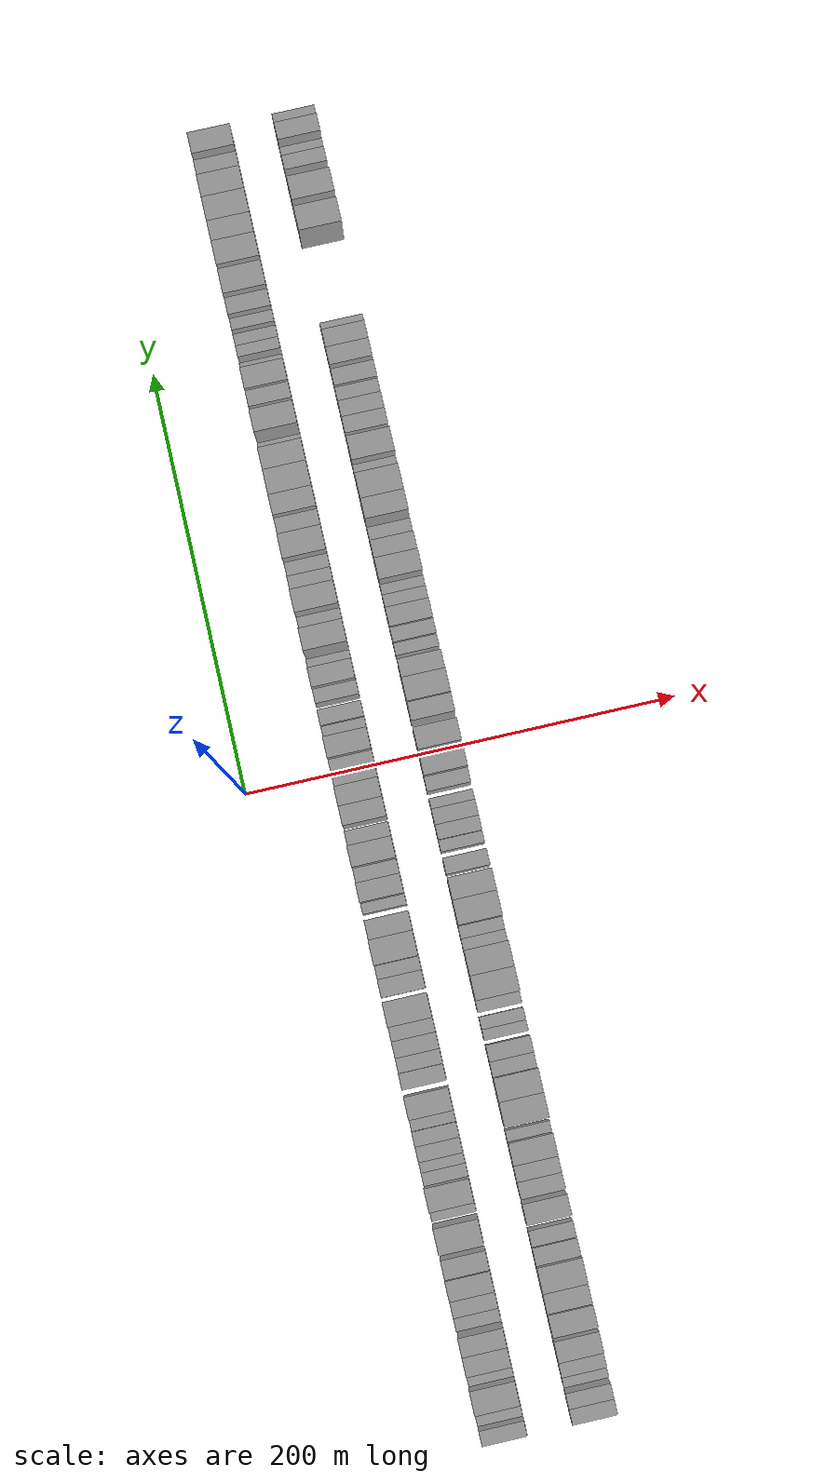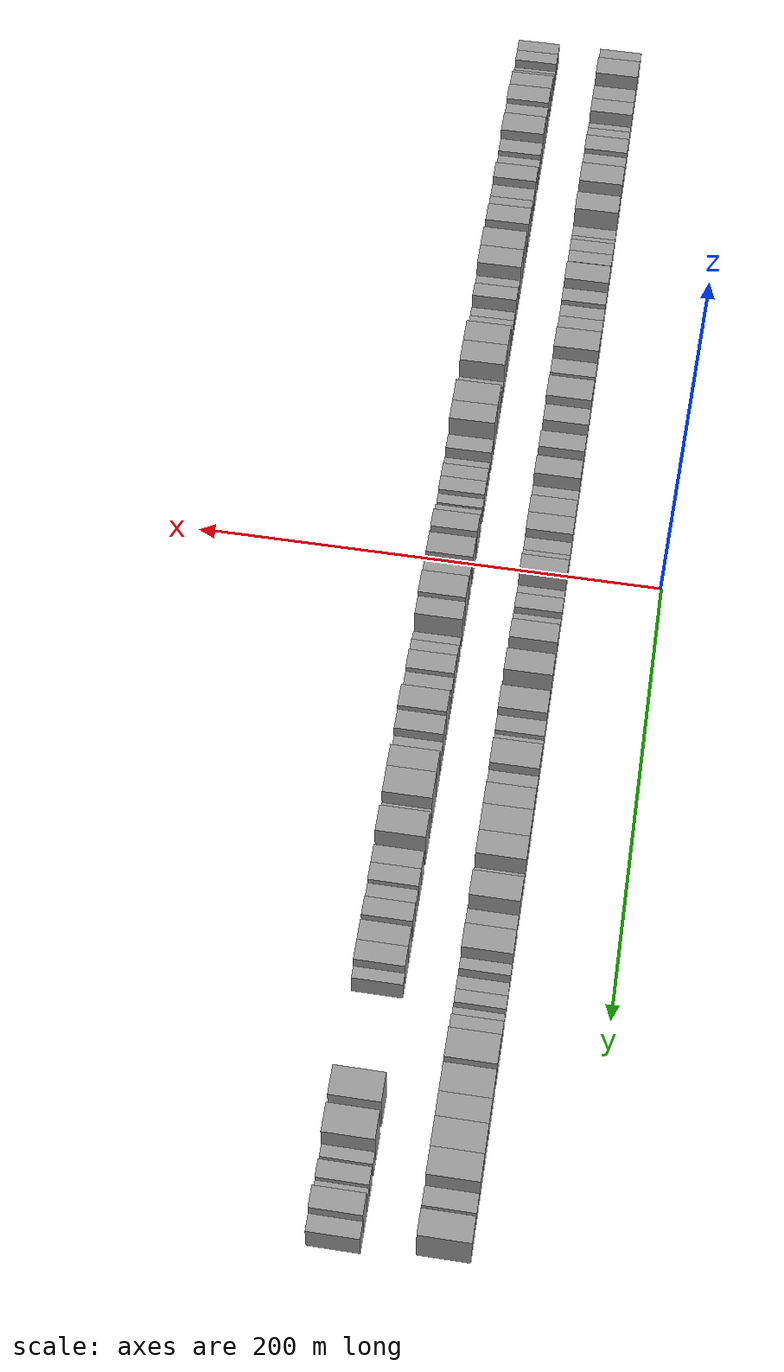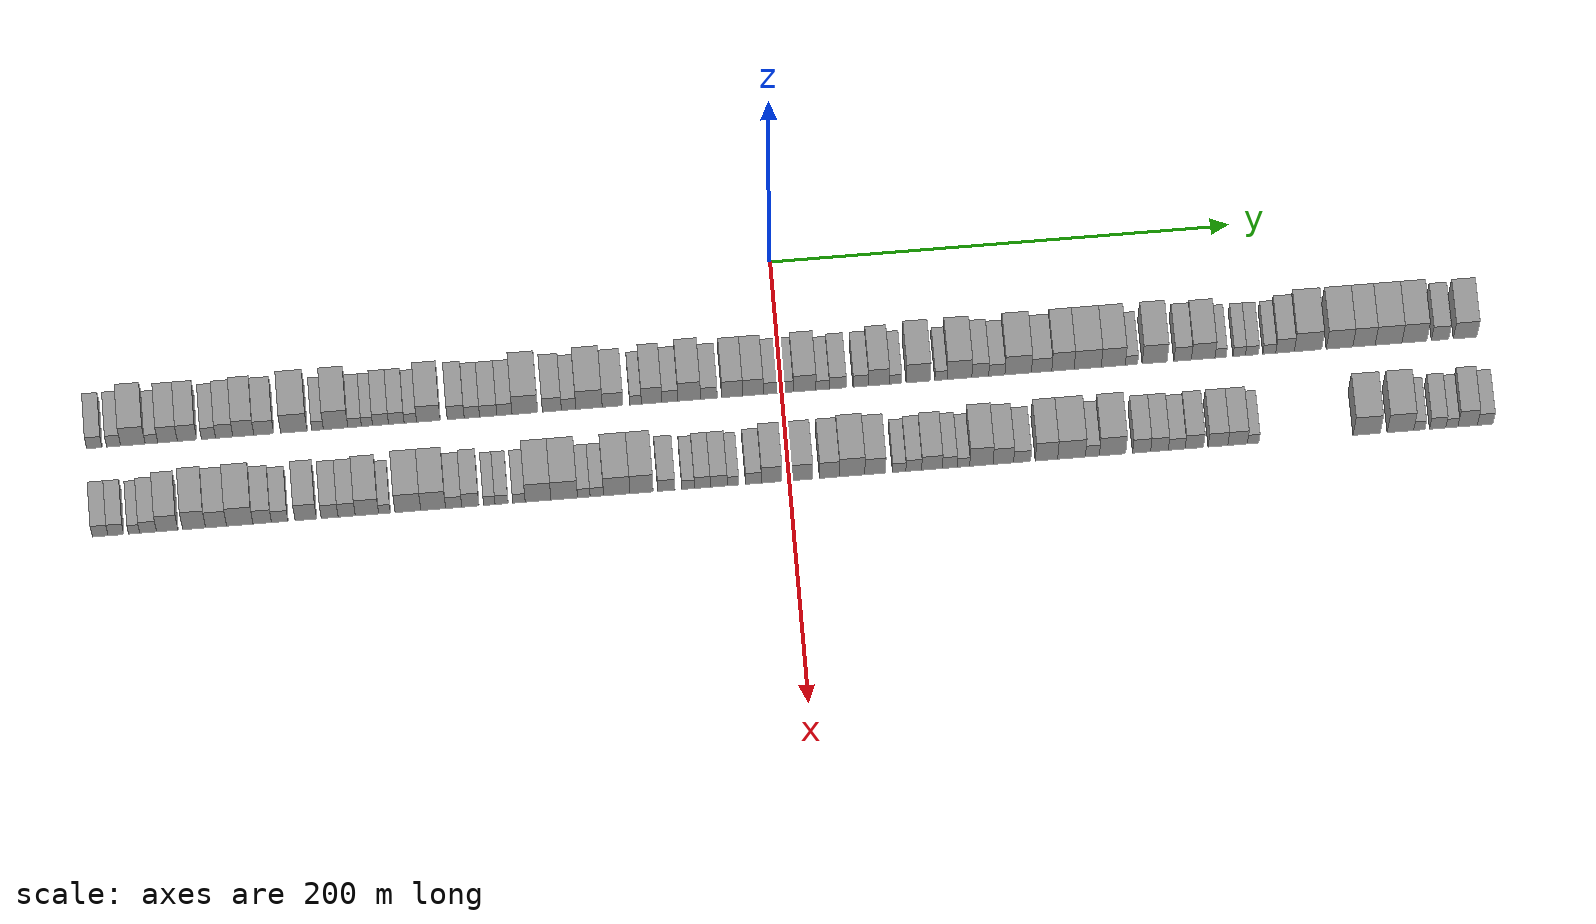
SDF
<sdf version="1.6">
 <world name="default">
  <scene>
   <sky><clouds><speed>12</speed></clouds></sky>
   <ambient>0.4 0.4 0.4 1</ambient>
   <background>0.7 0.7 0.7 1</background>
   <shadows>1</shadows>
  </scene>
  <gravity>0 0 -9.8066</gravity>
  <magnetic_field>6e-06 2.3e-05 -4.2e-05</magnetic_field>
  <physics default="0" name="default_physics" type="ode">
   <ode>
    <solver>
     <type>quick</type>
     <iters>10</iters>
     <sor>1.0</sor>
     <use_dynamic_moi_rescaling>0</use_dynamic_moi_rescaling>
    </solver>
    <constraints>
     <cfm>0</cfm>
     <erp>0.2</erp>
     <contact_max_correcting_vel>100</contact_max_correcting_vel>
     <contact_surface_layer>0.001</contact_surface_layer>
    </constraints>
   </ode>
   <max_step_size>0.004</max_step_size>
   <real_time_factor>1</real_time_factor>
   <real_time_update_rate>250</real_time_update_rate>
  </physics>
  <light name="sun" type="directional">
   <pose>0 0 10 0 0 0</pose>
   <diffuse>0.8 0.8 0.8 1</diffuse>
   <specular>0.2 0.2 0.2 1</specular>
   <attenuation>
    <range>1000</range>
    <constant>0.9</constant>
    <linear>0.01</linear>
    <quadratic>0.001</quadratic>
   </attenuation>
   <direction>-0.5 0.1 -0.9</direction>
  </light>
  <model name="building_1">
   <static>1</static>
   <pose>50.0000 -296.6885 0 0.000000 0.000000 0.000000</pose>
   <link name="link">
    <pose>0 0 7.50 0 0 0</pose>
    <collision name="collision"><geometry><box><size>20.0000 6.6230 15.0000</size></box></geometry></collision>
    <visual name="visual">
     <cast_shadows>0</cast_shadows>
     <geometry><box><size>20.0000 6.6230 15.0000</size></box></geometry>
     <material>
      <script>
       <uri>model://grey_wall/materials/scripts</uri>
       <uri>model://grey_wall/materials/textures</uri>
       <name>vrc/grey_wall</name>
      </script>
     </material>
    </visual>
   </link>
  </model>
  <model name="building_2">
   <static>1</static>
   <pose>50.0000 -288.3620 0 0.000000 0.000000 0.000000</pose>
   <link name="link">
    <pose>0 0 7.50 0 0 0</pose>
    <collision name="collision"><geometry><box><size>20.0000 6.0301 15.0000</size></box></geometry></collision>
    <visual name="visual">
     <cast_shadows>0</cast_shadows>
     <geometry><box><size>20.0000 6.0301 15.0000</size></box></geometry>
     <material>
      <script>
       <uri>model://grey_wall/materials/scripts</uri>
       <uri>model://grey_wall/materials/textures</uri>
       <name>vrc/grey_wall</name>
      </script>
     </material>
    </visual>
   </link>
  </model>
  <model name="building_3">
   <static>1</static>
   <pose>50.0000 -280.0617 0 0.000000 0.000000 0.000000</pose>
   <link name="link">
    <pose>0 0 12.00 0 0 0</pose>
    <collision name="collision"><geometry><box><size>20.0000 10.5706 24.0000</size></box></geometry></collision>
    <visual name="visual">
     <cast_shadows>0</cast_shadows>
     <geometry><box><size>20.0000 10.5706 24.0000</size></box></geometry>
     <material>
      <script>
       <uri>model://grey_wall/materials/scripts</uri>
       <uri>model://grey_wall/materials/textures</uri>
       <name>vrc/grey_wall</name>
      </script>
     </material>
    </visual>
   </link>
  </model>
  <model name="building_4">
   <static>1</static>
   <pose>50.0000 -272.0623 0 0.000000 0.000000 0.000000</pose>
   <link name="link">
    <pose>0 0 6.00 0 0 0</pose>
    <collision name="collision"><geometry><box><size>20.0000 5.4283 12.0000</size></box></geometry></collision>
    <visual name="visual">
     <cast_shadows>0</cast_shadows>
     <geometry><box><size>20.0000 5.4283 12.0000</size></box></geometry>
     <material>
      <script>
       <uri>model://grey_wall/materials/scripts</uri>
       <uri>model://grey_wall/materials/textures</uri>
       <name>vrc/grey_wall</name>
      </script>
     </material>
    </visual>
   </link>
  </model>
  <model name="building_5">
   <static>1</static>
   <pose>50.0000 -265.1304 0 0.000000 0.000000 0.000000</pose>
   <link name="link">
    <pose>0 0 10.50 0 0 0</pose>
    <collision name="collision"><geometry><box><size>20.0000 8.4354 21.0000</size></box></geometry></collision>
    <visual name="visual">
     <cast_shadows>0</cast_shadows>
     <geometry><box><size>20.0000 8.4354 21.0000</size></box></geometry>
     <material>
      <script>
       <uri>model://grey_wall/materials/scripts</uri>
       <uri>model://grey_wall/materials/textures</uri>
       <name>vrc/grey_wall</name>
      </script>
     </material>
    </visual>
   </link>
  </model>
  <model name="building_6">
   <static>1</static>
   <pose>50.0000 -256.7108 0 0.000000 0.000000 0.000000</pose>
   <link name="link">
    <pose>0 0 10.50 0 0 0</pose>
    <collision name="collision"><geometry><box><size>20.0000 8.4038 21.0000</size></box></geometry></collision>
    <visual name="visual">
     <cast_shadows>0</cast_shadows>
     <geometry><box><size>20.0000 8.4038 21.0000</size></box></geometry>
     <material>
      <script>
       <uri>model://grey_wall/materials/scripts</uri>
       <uri>model://grey_wall/materials/textures</uri>
       <name>vrc/grey_wall</name>
      </script>
     </material>
    </visual>
   </link>
  </model>
  <model name="building_7">
   <static>1</static>
   <pose>50.0000 -247.4542 0 0.000000 0.000000 0.000000</pose>
   <link name="link">
    <pose>0 0 7.50 0 0 0</pose>
    <collision name="collision"><geometry><box><size>20.0000 6.1095 15.0000</size></box></geometry></collision>
    <visual name="visual">
     <cast_shadows>0</cast_shadows>
     <geometry><box><size>20.0000 6.1095 15.0000</size></box></geometry>
     <material>
      <script>
       <uri>model://grey_wall/materials/scripts</uri>
       <uri>model://grey_wall/materials/textures</uri>
       <name>vrc/grey_wall</name>
      </script>
     </material>
    </visual>
   </link>
  </model>
  <model name="building_8">
   <static>1</static>
   <pose>50.0000 -240.6647 0 0.000000 0.000000 0.000000</pose>
   <link name="link">
    <pose>0 0 9.00 0 0 0</pose>
    <collision name="collision"><geometry><box><size>20.0000 7.4693 18.0000</size></box></geometry></collision>
    <visual name="visual">
     <cast_shadows>0</cast_shadows>
     <geometry><box><size>20.0000 7.4693 18.0000</size></box></geometry>
     <material>
      <script>
       <uri>model://grey_wall/materials/scripts</uri>
       <uri>model://grey_wall/materials/textures</uri>
       <name>vrc/grey_wall</name>
      </script>
     </material>
    </visual>
   </link>
  </model>
  <model name="building_9">
   <static>1</static>
   <pose>50.0000 -232.4220 0 0.000000 0.000000 0.000000</pose>
   <link name="link">
    <pose>0 0 10.50 0 0 0</pose>
    <collision name="collision"><geometry><box><size>20.0000 9.0161 21.0000</size></box></geometry></collision>
    <visual name="visual">
     <cast_shadows>0</cast_shadows>
     <geometry><box><size>20.0000 9.0161 21.0000</size></box></geometry>
     <material>
      <script>
       <uri>model://grey_wall/materials/scripts</uri>
       <uri>model://grey_wall/materials/textures</uri>
       <name>vrc/grey_wall</name>
      </script>
     </material>
    </visual>
   </link>
  </model>
  <model name="building_10">
   <static>1</static>
   <pose>50.0000 -223.6112 0 0.000000 0.000000 0.000000</pose>
   <link name="link">
    <pose>0 0 9.00 0 0 0</pose>
    <collision name="collision"><geometry><box><size>20.0000 8.6056 18.0000</size></box></geometry></collision>
    <visual name="visual">
     <cast_shadows>0</cast_shadows>
     <geometry><box><size>20.0000 8.6056 18.0000</size></box></geometry>
     <material>
      <script>
       <uri>model://grey_wall/materials/scripts</uri>
       <uri>model://grey_wall/materials/textures</uri>
       <name>vrc/grey_wall</name>
      </script>
     </material>
    </visual>
   </link>
  </model>
  <model name="building_11">
   <static>1</static>
   <pose>50.0000 -210.5880 0 0.000000 0.000000 0.000000</pose>
   <link name="link">
    <pose>0 0 12.00 0 0 0</pose>
    <collision name="collision"><geometry><box><size>20.0000 11.4408 24.0000</size></box></geometry></collision>
    <visual name="visual">
     <cast_shadows>0</cast_shadows>
     <geometry><box><size>20.0000 11.4408 24.0000</size></box></geometry>
     <material>
      <script>
       <uri>model://grey_wall/materials/scripts</uri>
       <uri>model://grey_wall/materials/textures</uri>
       <name>vrc/grey_wall</name>
      </script>
     </material>
    </visual>
   </link>
  </model>
  <model name="building_12">
   <static>1</static>
   <pose>50.0000 -200.3734 0 0.000000 0.000000 0.000000</pose>
   <link name="link">
    <pose>0 0 6.00 0 0 0</pose>
    <collision name="collision"><geometry><box><size>20.0000 4.9884 12.0000</size></box></geometry></collision>
    <visual name="visual">
     <cast_shadows>0</cast_shadows>
     <geometry><box><size>20.0000 4.9884 12.0000</size></box></geometry>
     <material>
      <script>
       <uri>model://grey_wall/materials/scripts</uri>
       <uri>model://grey_wall/materials/textures</uri>
       <name>vrc/grey_wall</name>
      </script>
     </material>
    </visual>
   </link>
  </model>
  <model name="building_13">
   <static>1</static>
   <pose>50.0000 -192.5975 0 0.000000 0.000000 0.000000</pose>
   <link name="link">
    <pose>0 0 12.00 0 0 0</pose>
    <collision name="collision"><geometry><box><size>20.0000 10.5634 24.0000</size></box></geometry></collision>
    <visual name="visual">
     <cast_shadows>0</cast_shadows>
     <geometry><box><size>20.0000 10.5634 24.0000</size></box></geometry>
     <material>
      <script>
       <uri>model://grey_wall/materials/scripts</uri>
       <uri>model://grey_wall/materials/textures</uri>
       <name>vrc/grey_wall</name>
      </script>
     </material>
    </visual>
   </link>
  </model>
  <model name="building_14">
   <static>1</static>
   <pose>50.0000 -184.3863 0 0.000000 0.000000 0.000000</pose>
   <link name="link">
    <pose>0 0 6.00 0 0 0</pose>
    <collision name="collision"><geometry><box><size>20.0000 5.8589 12.0000</size></box></geometry></collision>
    <visual name="visual">
     <cast_shadows>0</cast_shadows>
     <geometry><box><size>20.0000 5.8589 12.0000</size></box></geometry>
     <material>
      <script>
       <uri>model://grey_wall/materials/scripts</uri>
       <uri>model://grey_wall/materials/textures</uri>
       <name>vrc/grey_wall</name>
      </script>
     </material>
    </visual>
   </link>
  </model>
  <model name="building_15">
   <static>1</static>
   <pose>50.0000 -179.0469 0 0.000000 0.000000 0.000000</pose>
   <link name="link">
    <pose>0 0 6.00 0 0 0</pose>
    <collision name="collision"><geometry><box><size>20.0000 4.8199 12.0000</size></box></geometry></collision>
    <visual name="visual">
     <cast_shadows>0</cast_shadows>
     <geometry><box><size>20.0000 4.8199 12.0000</size></box></geometry>
     <material>
      <script>
       <uri>model://grey_wall/materials/scripts</uri>
       <uri>model://grey_wall/materials/textures</uri>
       <name>vrc/grey_wall</name>
      </script>
     </material>
    </visual>
   </link>
  </model>
  <model name="building_16">
   <static>1</static>
   <pose>50.0000 -173.2022 0 0.000000 0.000000 0.000000</pose>
   <link name="link">
    <pose>0 0 7.50 0 0 0</pose>
    <collision name="collision"><geometry><box><size>20.0000 6.8695 15.0000</size></box></geometry></collision>
    <visual name="visual">
     <cast_shadows>0</cast_shadows>
     <geometry><box><size>20.0000 6.8695 15.0000</size></box></geometry>
     <material>
      <script>
       <uri>model://grey_wall/materials/scripts</uri>
       <uri>model://grey_wall/materials/textures</uri>
       <name>vrc/grey_wall</name>
      </script>
     </material>
    </visual>
   </link>
  </model>
  <model name="building_17">
   <static>1</static>
   <pose>50.0000 -166.3987 0 0.000000 0.000000 0.000000</pose>
   <link name="link">
    <pose>0 0 7.50 0 0 0</pose>
    <collision name="collision"><geometry><box><size>20.0000 6.7375 15.0000</size></box></geometry></collision>
    <visual name="visual">
     <cast_shadows>0</cast_shadows>
     <geometry><box><size>20.0000 6.7375 15.0000</size></box></geometry>
     <material>
      <script>
       <uri>model://grey_wall/materials/scripts</uri>
       <uri>model://grey_wall/materials/textures</uri>
       <name>vrc/grey_wall</name>
      </script>
     </material>
    </visual>
   </link>
  </model>
  <model name="building_18">
   <static>1</static>
   <pose>50.0000 -160.3382 0 0.000000 0.000000 0.000000</pose>
   <link name="link">
    <pose>0 0 6.00 0 0 0</pose>
    <collision name="collision"><geometry><box><size>20.0000 5.3836 12.0000</size></box></geometry></collision>
    <visual name="visual">
     <cast_shadows>0</cast_shadows>
     <geometry><box><size>20.0000 5.3836 12.0000</size></box></geometry>
     <material>
      <script>
       <uri>model://grey_wall/materials/scripts</uri>
       <uri>model://grey_wall/materials/textures</uri>
       <name>vrc/grey_wall</name>
      </script>
     </material>
    </visual>
   </link>
  </model>
  <model name="building_19">
   <static>1</static>
   <pose>50.0000 -152.5379 0 0.000000 0.000000 0.000000</pose>
   <link name="link">
    <pose>0 0 10.50 0 0 0</pose>
    <collision name="collision"><geometry><box><size>20.0000 10.2169 21.0000</size></box></geometry></collision>
    <visual name="visual">
     <cast_shadows>0</cast_shadows>
     <geometry><box><size>20.0000 10.2169 21.0000</size></box></geometry>
     <material>
      <script>
       <uri>model://grey_wall/materials/scripts</uri>
       <uri>model://grey_wall/materials/textures</uri>
       <name>vrc/grey_wall</name>
      </script>
     </material>
    </visual>
   </link>
  </model>
  <model name="building_20">
   <static>1</static>
   <pose>50.0000 -140.7520 0 0.000000 0.000000 0.000000</pose>
   <link name="link">
    <pose>0 0 9.00 0 0 0</pose>
    <collision name="collision"><geometry><box><size>20.0000 7.3550 18.0000</size></box></geometry></collision>
    <visual name="visual">
     <cast_shadows>0</cast_shadows>
     <geometry><box><size>20.0000 7.3550 18.0000</size></box></geometry>
     <material>
      <script>
       <uri>model://grey_wall/materials/scripts</uri>
       <uri>model://grey_wall/materials/textures</uri>
       <name>vrc/grey_wall</name>
      </script>
     </material>
    </visual>
   </link>
  </model>
  <model name="building_21">
   <static>1</static>
   <pose>50.0000 -133.7475 0 0.000000 0.000000 0.000000</pose>
   <link name="link">
    <pose>0 0 7.50 0 0 0</pose>
    <collision name="collision"><geometry><box><size>20.0000 6.6540 15.0000</size></box></geometry></collision>
    <visual name="visual">
     <cast_shadows>0</cast_shadows>
     <geometry><box><size>20.0000 6.6540 15.0000</size></box></geometry>
     <material>
      <script>
       <uri>model://grey_wall/materials/scripts</uri>
       <uri>model://grey_wall/materials/textures</uri>
       <name>vrc/grey_wall</name>
      </script>
     </material>
    </visual>
   </link>
  </model>
  <model name="building_22">
   <static>1</static>
   <pose>50.0000 -126.6959 0 0.000000 0.000000 0.000000</pose>
   <link name="link">
    <pose>0 0 7.50 0 0 0</pose>
    <collision name="collision"><geometry><box><size>20.0000 7.4490 15.0000</size></box></geometry></collision>
    <visual name="visual">
     <cast_shadows>0</cast_shadows>
     <geometry><box><size>20.0000 7.4490 15.0000</size></box></geometry>
     <material>
      <script>
       <uri>model://grey_wall/materials/scripts</uri>
       <uri>model://grey_wall/materials/textures</uri>
       <name>vrc/grey_wall</name>
      </script>
     </material>
    </visual>
   </link>
  </model>
  <model name="building_23">
   <static>1</static>
   <pose>50.0000 -119.7036 0 0.000000 0.000000 0.000000</pose>
   <link name="link">
    <pose>0 0 7.50 0 0 0</pose>
    <collision name="collision"><geometry><box><size>20.0000 6.5356 15.0000</size></box></geometry></collision>
    <visual name="visual">
     <cast_shadows>0</cast_shadows>
     <geometry><box><size>20.0000 6.5356 15.0000</size></box></geometry>
     <material>
      <script>
       <uri>model://grey_wall/materials/scripts</uri>
       <uri>model://grey_wall/materials/textures</uri>
       <name>vrc/grey_wall</name>
      </script>
     </material>
    </visual>
   </link>
  </model>
  <model name="building_24">
   <static>1</static>
   <pose>50.0000 -110.8735 0 0.000000 0.000000 0.000000</pose>
   <link name="link">
    <pose>0 0 12.00 0 0 0</pose>
    <collision name="collision"><geometry><box><size>20.0000 11.1247 24.0000</size></box></geometry></collision>
    <visual name="visual">
     <cast_shadows>0</cast_shadows>
     <geometry><box><size>20.0000 11.1247 24.0000</size></box></geometry>
     <material>
      <script>
       <uri>model://grey_wall/materials/scripts</uri>
       <uri>model://grey_wall/materials/textures</uri>
       <name>vrc/grey_wall</name>
      </script>
     </material>
    </visual>
   </link>
  </model>
  <model name="building_25">
   <static>1</static>
   <pose>50.0000 -99.2027 0 0.000000 0.000000 0.000000</pose>
   <link name="link">
    <pose>0 0 9.00 0 0 0</pose>
    <collision name="collision"><geometry><box><size>20.0000 8.2169 18.0000</size></box></geometry></collision>
    <visual name="visual">
     <cast_shadows>0</cast_shadows>
     <geometry><box><size>20.0000 8.2169 18.0000</size></box></geometry>
     <material>
      <script>
       <uri>model://grey_wall/materials/scripts</uri>
       <uri>model://grey_wall/materials/textures</uri>
       <name>vrc/grey_wall</name>
      </script>
     </material>
    </visual>
   </link>
  </model>
  <model name="building_26">
   <static>1</static>
   <pose>50.0000 -91.9882 0 0.000000 0.000000 0.000000</pose>
   <link name="link">
    <pose>0 0 7.50 0 0 0</pose>
    <collision name="collision"><geometry><box><size>20.0000 6.2121 15.0000</size></box></geometry></collision>
    <visual name="visual">
     <cast_shadows>0</cast_shadows>
     <geometry><box><size>20.0000 6.2121 15.0000</size></box></geometry>
     <material>
      <script>
       <uri>model://grey_wall/materials/scripts</uri>
       <uri>model://grey_wall/materials/textures</uri>
       <name>vrc/grey_wall</name>
      </script>
     </material>
    </visual>
   </link>
  </model>
  <model name="building_27">
   <static>1</static>
   <pose>50.0000 -83.1758 0 0.000000 0.000000 0.000000</pose>
   <link name="link">
    <pose>0 0 12.00 0 0 0</pose>
    <collision name="collision"><geometry><box><size>20.0000 11.4127 24.0000</size></box></geometry></collision>
    <visual name="visual">
     <cast_shadows>0</cast_shadows>
     <geometry><box><size>20.0000 11.4127 24.0000</size></box></geometry>
     <material>
      <script>
       <uri>model://grey_wall/materials/scripts</uri>
       <uri>model://grey_wall/materials/textures</uri>
       <name>vrc/grey_wall</name>
      </script>
     </material>
    </visual>
   </link>
  </model>
  <model name="building_28">
   <static>1</static>
   <pose>50.0000 -72.9829 0 0.000000 0.000000 0.000000</pose>
   <link name="link">
    <pose>0 0 9.00 0 0 0</pose>
    <collision name="collision"><geometry><box><size>20.0000 8.9731 18.0000</size></box></geometry></collision>
    <visual name="visual">
     <cast_shadows>0</cast_shadows>
     <geometry><box><size>20.0000 8.9731 18.0000</size></box></geometry>
     <material>
      <script>
       <uri>model://grey_wall/materials/scripts</uri>
       <uri>model://grey_wall/materials/textures</uri>
       <name>vrc/grey_wall</name>
      </script>
     </material>
    </visual>
   </link>
  </model>
  <model name="building_29">
   <static>1</static>
   <pose>50.0000 -63.0117 0 0.000000 0.000000 0.000000</pose>
   <link name="link">
    <pose>0 0 6.00 0 0 0</pose>
    <collision name="collision"><geometry><box><size>20.0000 4.9692 12.0000</size></box></geometry></collision>
    <visual name="visual">
     <cast_shadows>0</cast_shadows>
     <geometry><box><size>20.0000 4.9692 12.0000</size></box></geometry>
     <material>
      <script>
       <uri>model://grey_wall/materials/scripts</uri>
       <uri>model://grey_wall/materials/textures</uri>
       <name>vrc/grey_wall</name>
      </script>
     </material>
    </visual>
   </link>
  </model>
  <model name="building_30">
   <static>1</static>
   <pose>50.0000 -56.1043 0 0.000000 0.000000 0.000000</pose>
   <link name="link">
    <pose>0 0 10.50 0 0 0</pose>
    <collision name="collision"><geometry><box><size>20.0000 8.8454 21.0000</size></box></geometry></collision>
    <visual name="visual">
     <cast_shadows>0</cast_shadows>
     <geometry><box><size>20.0000 8.8454 21.0000</size></box></geometry>
     <material>
      <script>
       <uri>model://grey_wall/materials/scripts</uri>
       <uri>model://grey_wall/materials/textures</uri>
       <name>vrc/grey_wall</name>
      </script>
     </material>
    </visual>
   </link>
  </model>
  <model name="building_31">
   <static>1</static>
   <pose>50.0000 -48.2163 0 0.000000 0.000000 0.000000</pose>
   <link name="link">
    <pose>0 0 7.50 0 0 0</pose>
    <collision name="collision"><geometry><box><size>20.0000 6.9306 15.0000</size></box></geometry></collision>
    <visual name="visual">
     <cast_shadows>0</cast_shadows>
     <geometry><box><size>20.0000 6.9306 15.0000</size></box></geometry>
     <material>
      <script>
       <uri>model://grey_wall/materials/scripts</uri>
       <uri>model://grey_wall/materials/textures</uri>
       <name>vrc/grey_wall</name>
      </script>
     </material>
    </visual>
   </link>
  </model>
  <model name="building_32">
   <static>1</static>
   <pose>50.0000 -39.8728 0 0.000000 0.000000 0.000000</pose>
   <link name="link">
    <pose>0 0 12.00 0 0 0</pose>
    <collision name="collision"><geometry><box><size>20.0000 9.7566 24.0000</size></box></geometry></collision>
    <visual name="visual">
     <cast_shadows>0</cast_shadows>
     <geometry><box><size>20.0000 9.7566 24.0000</size></box></geometry>
     <material>
      <script>
       <uri>model://grey_wall/materials/scripts</uri>
       <uri>model://grey_wall/materials/textures</uri>
       <name>vrc/grey_wall</name>
      </script>
     </material>
    </visual>
   </link>
  </model>
  <model name="building_33">
   <static>1</static>
   <pose>50.0000 -31.3710 0 0.000000 0.000000 0.000000</pose>
   <link name="link">
    <pose>0 0 7.50 0 0 0</pose>
    <collision name="collision"><geometry><box><size>20.0000 7.2471 15.0000</size></box></geometry></collision>
    <visual name="visual">
     <cast_shadows>0</cast_shadows>
     <geometry><box><size>20.0000 7.2471 15.0000</size></box></geometry>
     <material>
      <script>
       <uri>model://grey_wall/materials/scripts</uri>
       <uri>model://grey_wall/materials/textures</uri>
       <name>vrc/grey_wall</name>
      </script>
     </material>
    </visual>
   </link>
  </model>
  <model name="building_34">
   <static>1</static>
   <pose>50.0000 -21.2676 0 0.000000 0.000000 0.000000</pose>
   <link name="link">
    <pose>0 0 10.50 0 0 0</pose>
    <collision name="collision"><geometry><box><size>20.0000 8.9597 21.0000</size></box></geometry></collision>
    <visual name="visual">
     <cast_shadows>0</cast_shadows>
     <geometry><box><size>20.0000 8.9597 21.0000</size></box></geometry>
     <material>
      <script>
       <uri>model://grey_wall/materials/scripts</uri>
       <uri>model://grey_wall/materials/textures</uri>
       <name>vrc/grey_wall</name>
      </script>
     </material>
    </visual>
   </link>
  </model>
  <model name="building_35">
   <static>1</static>
   <pose>50.0000 -12.3017 0 0.000000 0.000000 0.000000</pose>
   <link name="link">
    <pose>0 0 10.50 0 0 0</pose>
    <collision name="collision"><geometry><box><size>20.0000 8.9721 21.0000</size></box></geometry></collision>
    <visual name="visual">
     <cast_shadows>0</cast_shadows>
     <geometry><box><size>20.0000 8.9721 21.0000</size></box></geometry>
     <material>
      <script>
       <uri>model://grey_wall/materials/scripts</uri>
       <uri>model://grey_wall/materials/textures</uri>
       <name>vrc/grey_wall</name>
      </script>
     </material>
    </visual>
   </link>
  </model>
  <model name="building_36">
   <static>1</static>
   <pose>50.0000 -4.4959 0 0.000000 0.000000 0.000000</pose>
   <link name="link">
    <pose>0 0 7.50 0 0 0</pose>
    <collision name="collision"><geometry><box><size>20.0000 6.6396 15.0000</size></box></geometry></collision>
    <visual name="visual">
     <cast_shadows>0</cast_shadows>
     <geometry><box><size>20.0000 6.6396 15.0000</size></box></geometry>
     <material>
      <script>
       <uri>model://grey_wall/materials/scripts</uri>
       <uri>model://grey_wall/materials/textures</uri>
       <name>vrc/grey_wall</name>
      </script>
     </material>
    </visual>
   </link>
  </model>
  <model name="building_37">
   <static>1</static>
   <pose>50.0000 2.0016 0 0.000000 0.000000 0.000000</pose>
   <link name="link">
    <pose>0 0 7.50 0 0 0</pose>
    <collision name="collision"><geometry><box><size>20.0000 6.3552 15.0000</size></box></geometry></collision>
    <visual name="visual">
     <cast_shadows>0</cast_shadows>
     <geometry><box><size>20.0000 6.3552 15.0000</size></box></geometry>
     <material>
      <script>
       <uri>model://grey_wall/materials/scripts</uri>
       <uri>model://grey_wall/materials/textures</uri>
       <name>vrc/grey_wall</name>
      </script>
     </material>
    </visual>
   </link>
  </model>
  <model name="building_38">
   <static>1</static>
   <pose>50.0000 10.0908 0 0.000000 0.000000 0.000000</pose>
   <link name="link">
    <pose>0 0 10.50 0 0 0</pose>
    <collision name="collision"><geometry><box><size>20.0000 9.8233 21.0000</size></box></geometry></collision>
    <visual name="visual">
     <cast_shadows>0</cast_shadows>
     <geometry><box><size>20.0000 9.8233 21.0000</size></box></geometry>
     <material>
      <script>
       <uri>model://grey_wall/materials/scripts</uri>
       <uri>model://grey_wall/materials/textures</uri>
       <name>vrc/grey_wall</name>
      </script>
     </material>
    </visual>
   </link>
  </model>
  <model name="building_39">
   <static>1</static>
   <pose>50.0000 17.8913 0 0.000000 0.000000 0.000000</pose>
   <link name="link">
    <pose>0 0 6.00 0 0 0</pose>
    <collision name="collision"><geometry><box><size>20.0000 5.7777 12.0000</size></box></geometry></collision>
    <visual name="visual">
     <cast_shadows>0</cast_shadows>
     <geometry><box><size>20.0000 5.7777 12.0000</size></box></geometry>
     <material>
      <script>
       <uri>model://grey_wall/materials/scripts</uri>
       <uri>model://grey_wall/materials/textures</uri>
       <name>vrc/grey_wall</name>
      </script>
     </material>
    </visual>
   </link>
  </model>
  <model name="building_40">
   <static>1</static>
   <pose>50.0000 24.4286 0 0.000000 0.000000 0.000000</pose>
   <link name="link">
    <pose>0 0 7.50 0 0 0</pose>
    <collision name="collision"><geometry><box><size>20.0000 7.2970 15.0000</size></box></geometry></collision>
    <visual name="visual">
     <cast_shadows>0</cast_shadows>
     <geometry><box><size>20.0000 7.2970 15.0000</size></box></geometry>
     <material>
      <script>
       <uri>model://grey_wall/materials/scripts</uri>
       <uri>model://grey_wall/materials/textures</uri>
       <name>vrc/grey_wall</name>
      </script>
     </material>
    </visual>
   </link>
  </model>
  <model name="building_41">
   <static>1</static>
   <pose>50.0000 34.3968 0 0.000000 0.000000 0.000000</pose>
   <link name="link">
    <pose>0 0 7.50 0 0 0</pose>
    <collision name="collision"><geometry><box><size>20.0000 6.6393 15.0000</size></box></geometry></collision>
    <visual name="visual">
     <cast_shadows>0</cast_shadows>
     <geometry><box><size>20.0000 6.6393 15.0000</size></box></geometry>
     <material>
      <script>
       <uri>model://grey_wall/materials/scripts</uri>
       <uri>model://grey_wall/materials/textures</uri>
       <name>vrc/grey_wall</name>
      </script>
     </material>
    </visual>
   </link>
  </model>
  <model name="building_42">
   <static>1</static>
   <pose>50.0000 42.2371 0 0.000000 0.000000 0.000000</pose>
   <link name="link">
    <pose>0 0 10.50 0 0 0</pose>
    <collision name="collision"><geometry><box><size>20.0000 9.0413 21.0000</size></box></geometry></collision>
    <visual name="visual">
     <cast_shadows>0</cast_shadows>
     <geometry><box><size>20.0000 9.0413 21.0000</size></box></geometry>
     <material>
      <script>
       <uri>model://grey_wall/materials/scripts</uri>
       <uri>model://grey_wall/materials/textures</uri>
       <name>vrc/grey_wall</name>
      </script>
     </material>
    </visual>
   </link>
  </model>
  <model name="building_43">
   <static>1</static>
   <pose>50.0000 49.4258 0 0.000000 0.000000 0.000000</pose>
   <link name="link">
    <pose>0 0 6.00 0 0 0</pose>
    <collision name="collision"><geometry><box><size>20.0000 5.3360 12.0000</size></box></geometry></collision>
    <visual name="visual">
     <cast_shadows>0</cast_shadows>
     <geometry><box><size>20.0000 5.3360 12.0000</size></box></geometry>
     <material>
      <script>
       <uri>model://grey_wall/materials/scripts</uri>
       <uri>model://grey_wall/materials/textures</uri>
       <name>vrc/grey_wall</name>
      </script>
     </material>
    </visual>
   </link>
  </model>
  <model name="building_44">
   <static>1</static>
   <pose>50.0000 59.3077 0 0.000000 0.000000 0.000000</pose>
   <link name="link">
    <pose>0 0 12.00 0 0 0</pose>
    <collision name="collision"><geometry><box><size>20.0000 10.4279 24.0000</size></box></geometry></collision>
    <visual name="visual">
     <cast_shadows>0</cast_shadows>
     <geometry><box><size>20.0000 10.4279 24.0000</size></box></geometry>
     <material>
      <script>
       <uri>model://grey_wall/materials/scripts</uri>
       <uri>model://grey_wall/materials/textures</uri>
       <name>vrc/grey_wall</name>
      </script>
     </material>
    </visual>
   </link>
  </model>
  <model name="building_45">
   <static>1</static>
   <pose>50.0000 69.1614 0 0.000000 0.000000 0.000000</pose>
   <link name="link">
    <pose>0 0 6.00 0 0 0</pose>
    <collision name="collision"><geometry><box><size>20.0000 5.2795 12.0000</size></box></geometry></collision>
    <visual name="visual">
     <cast_shadows>0</cast_shadows>
     <geometry><box><size>20.0000 5.2795 12.0000</size></box></geometry>
     <material>
      <script>
       <uri>model://grey_wall/materials/scripts</uri>
       <uri>model://grey_wall/materials/textures</uri>
       <name>vrc/grey_wall</name>
      </script>
     </material>
    </visual>
   </link>
  </model>
  <model name="building_46">
   <static>1</static>
   <pose>50.0000 77.1668 0 0.000000 0.000000 0.000000</pose>
   <link name="link">
    <pose>0 0 12.00 0 0 0</pose>
    <collision name="collision"><geometry><box><size>20.0000 10.7313 24.0000</size></box></geometry></collision>
    <visual name="visual">
     <cast_shadows>0</cast_shadows>
     <geometry><box><size>20.0000 10.7313 24.0000</size></box></geometry>
     <material>
      <script>
       <uri>model://grey_wall/materials/scripts</uri>
       <uri>model://grey_wall/materials/textures</uri>
       <name>vrc/grey_wall</name>
      </script>
     </material>
    </visual>
   </link>
  </model>
  <model name="building_47">
   <static>1</static>
   <pose>50.0000 86.1929 0 0.000000 0.000000 0.000000</pose>
   <link name="link">
    <pose>0 0 9.00 0 0 0</pose>
    <collision name="collision"><geometry><box><size>20.0000 7.3210 18.0000</size></box></geometry></collision>
    <visual name="visual">
     <cast_shadows>0</cast_shadows>
     <geometry><box><size>20.0000 7.3210 18.0000</size></box></geometry>
     <material>
      <script>
       <uri>model://grey_wall/materials/scripts</uri>
       <uri>model://grey_wall/materials/textures</uri>
       <name>vrc/grey_wall</name>
      </script>
     </material>
    </visual>
   </link>
  </model>
  <model name="building_48">
   <static>1</static>
   <pose>50.0000 93.3614 0 0.000000 0.000000 0.000000</pose>
   <link name="link">
    <pose>0 0 7.50 0 0 0</pose>
    <collision name="collision"><geometry><box><size>20.0000 7.0160 15.0000</size></box></geometry></collision>
    <visual name="visual">
     <cast_shadows>0</cast_shadows>
     <geometry><box><size>20.0000 7.0160 15.0000</size></box></geometry>
     <material>
      <script>
       <uri>model://grey_wall/materials/scripts</uri>
       <uri>model://grey_wall/materials/textures</uri>
       <name>vrc/grey_wall</name>
      </script>
     </material>
    </visual>
   </link>
  </model>
  <model name="building_49">
   <static>1</static>
   <pose>50.0000 102.6188 0 0.000000 0.000000 0.000000</pose>
   <link name="link">
    <pose>0 0 12.00 0 0 0</pose>
    <collision name="collision"><geometry><box><size>20.0000 11.4986 24.0000</size></box></geometry></collision>
    <visual name="visual">
     <cast_shadows>0</cast_shadows>
     <geometry><box><size>20.0000 11.4986 24.0000</size></box></geometry>
     <material>
      <script>
       <uri>model://grey_wall/materials/scripts</uri>
       <uri>model://grey_wall/materials/textures</uri>
       <name>vrc/grey_wall</name>
      </script>
     </material>
    </visual>
   </link>
  </model>
  <model name="building_50">
   <static>1</static>
   <pose>50.0000 112.7771 0 0.000000 0.000000 0.000000</pose>
   <link name="link">
    <pose>0 0 9.00 0 0 0</pose>
    <collision name="collision"><geometry><box><size>20.0000 8.8180 18.0000</size></box></geometry></collision>
    <visual name="visual">
     <cast_shadows>0</cast_shadows>
     <geometry><box><size>20.0000 8.8180 18.0000</size></box></geometry>
     <material>
      <script>
       <uri>model://grey_wall/materials/scripts</uri>
       <uri>model://grey_wall/materials/textures</uri>
       <name>vrc/grey_wall</name>
      </script>
     </material>
    </visual>
   </link>
  </model>
  <model name="building_51">
   <static>1</static>
   <pose>50.0000 122.0197 0 0.000000 0.000000 0.000000</pose>
   <link name="link">
    <pose>0 0 12.00 0 0 0</pose>
    <collision name="collision"><geometry><box><size>20.0000 9.6673 24.0000</size></box></geometry></collision>
    <visual name="visual">
     <cast_shadows>0</cast_shadows>
     <geometry><box><size>20.0000 9.6673 24.0000</size></box></geometry>
     <material>
      <script>
       <uri>model://grey_wall/materials/scripts</uri>
       <uri>model://grey_wall/materials/textures</uri>
       <name>vrc/grey_wall</name>
      </script>
     </material>
    </visual>
   </link>
  </model>
  <model name="building_52">
   <static>1</static>
   <pose>50.0000 132.7473 0 0.000000 0.000000 0.000000</pose>
   <link name="link">
    <pose>0 0 12.00 0 0 0</pose>
    <collision name="collision"><geometry><box><size>20.0000 11.7878 24.0000</size></box></geometry></collision>
    <visual name="visual">
     <cast_shadows>0</cast_shadows>
     <geometry><box><size>20.0000 11.7878 24.0000</size></box></geometry>
     <material>
      <script>
       <uri>model://grey_wall/materials/scripts</uri>
       <uri>model://grey_wall/materials/textures</uri>
       <name>vrc/grey_wall</name>
      </script>
     </material>
    </visual>
   </link>
  </model>
  <model name="building_53">
   <static>1</static>
   <pose>50.0000 143.8439 0 0.000000 0.000000 0.000000</pose>
   <link name="link">
    <pose>0 0 12.00 0 0 0</pose>
    <collision name="collision"><geometry><box><size>20.0000 10.4054 24.0000</size></box></geometry></collision>
    <visual name="visual">
     <cast_shadows>0</cast_shadows>
     <geometry><box><size>20.0000 10.4054 24.0000</size></box></geometry>
     <material>
      <script>
       <uri>model://grey_wall/materials/scripts</uri>
       <uri>model://grey_wall/materials/textures</uri>
       <name>vrc/grey_wall</name>
      </script>
     </material>
    </visual>
   </link>
  </model>
  <model name="building_54">
   <static>1</static>
   <pose>50.0000 151.7143 0 0.000000 0.000000 0.000000</pose>
   <link name="link">
    <pose>0 0 6.00 0 0 0</pose>
    <collision name="collision"><geometry><box><size>20.0000 5.3353 12.0000</size></box></geometry></collision>
    <visual name="visual">
     <cast_shadows>0</cast_shadows>
     <geometry><box><size>20.0000 5.3353 12.0000</size></box></geometry>
     <material>
      <script>
       <uri>model://grey_wall/materials/scripts</uri>
       <uri>model://grey_wall/materials/textures</uri>
       <name>vrc/grey_wall</name>
      </script>
     </material>
    </visual>
   </link>
  </model>
  <model name="building_55">
   <static>1</static>
   <pose>50.0000 161.7649 0 0.000000 0.000000 0.000000</pose>
   <link name="link">
    <pose>0 0 12.00 0 0 0</pose>
    <collision name="collision"><geometry><box><size>20.0000 10.7659 24.0000</size></box></geometry></collision>
    <visual name="visual">
     <cast_shadows>0</cast_shadows>
     <geometry><box><size>20.0000 10.7659 24.0000</size></box></geometry>
     <material>
      <script>
       <uri>model://grey_wall/materials/scripts</uri>
       <uri>model://grey_wall/materials/textures</uri>
       <name>vrc/grey_wall</name>
      </script>
     </material>
    </visual>
   </link>
  </model>
  <model name="building_56">
   <static>1</static>
   <pose>50.0000 173.9387 0 0.000000 0.000000 0.000000</pose>
   <link name="link">
    <pose>0 0 9.00 0 0 0</pose>
    <collision name="collision"><geometry><box><size>20.0000 7.5818 18.0000</size></box></geometry></collision>
    <visual name="visual">
     <cast_shadows>0</cast_shadows>
     <geometry><box><size>20.0000 7.5818 18.0000</size></box></geometry>
     <material>
      <script>
       <uri>model://grey_wall/materials/scripts</uri>
       <uri>model://grey_wall/materials/textures</uri>
       <name>vrc/grey_wall</name>
      </script>
     </material>
    </visual>
   </link>
  </model>
  <model name="building_57">
   <static>1</static>
   <pose>50.0000 182.8425 0 0.000000 0.000000 0.000000</pose>
   <link name="link">
    <pose>0 0 10.50 0 0 0</pose>
    <collision name="collision"><geometry><box><size>20.0000 10.2259 21.0000</size></box></geometry></collision>
    <visual name="visual">
     <cast_shadows>0</cast_shadows>
     <geometry><box><size>20.0000 10.2259 21.0000</size></box></geometry>
     <material>
      <script>
       <uri>model://grey_wall/materials/scripts</uri>
       <uri>model://grey_wall/materials/textures</uri>
       <name>vrc/grey_wall</name>
      </script>
     </material>
    </visual>
   </link>
  </model>
  <model name="building_58">
   <static>1</static>
   <pose>50.0000 190.3737 0 0.000000 0.000000 0.000000</pose>
   <link name="link">
    <pose>0 0 6.00 0 0 0</pose>
    <collision name="collision"><geometry><box><size>20.0000 4.8365 12.0000</size></box></geometry></collision>
    <visual name="visual">
     <cast_shadows>0</cast_shadows>
     <geometry><box><size>20.0000 4.8365 12.0000</size></box></geometry>
     <material>
      <script>
       <uri>model://grey_wall/materials/scripts</uri>
       <uri>model://grey_wall/materials/textures</uri>
       <name>vrc/grey_wall</name>
      </script>
     </material>
    </visual>
   </link>
  </model>
  <model name="building_59">
   <static>1</static>
   <pose>50.0000 198.5047 0 0.000000 0.000000 0.000000</pose>
   <link name="link">
    <pose>0 0 6.00 0 0 0</pose>
    <collision name="collision"><geometry><box><size>20.0000 5.4254 12.0000</size></box></geometry></collision>
    <visual name="visual">
     <cast_shadows>0</cast_shadows>
     <geometry><box><size>20.0000 5.4254 12.0000</size></box></geometry>
     <material>
      <script>
       <uri>model://grey_wall/materials/scripts</uri>
       <uri>model://grey_wall/materials/textures</uri>
       <name>vrc/grey_wall</name>
      </script>
     </material>
    </visual>
   </link>
  </model>
  <model name="building_60">
   <static>1</static>
   <pose>50.0000 203.9875 0 0.000000 0.000000 0.000000</pose>
   <link name="link">
    <pose>0 0 6.00 0 0 0</pose>
    <collision name="collision"><geometry><box><size>20.0000 5.5404 12.0000</size></box></geometry></collision>
    <visual name="visual">
     <cast_shadows>0</cast_shadows>
     <geometry><box><size>20.0000 5.5404 12.0000</size></box></geometry>
     <material>
      <script>
       <uri>model://grey_wall/materials/scripts</uri>
       <uri>model://grey_wall/materials/textures</uri>
       <name>vrc/grey_wall</name>
      </script>
     </material>
    </visual>
   </link>
  </model>
  <model name="building_61">
   <static>1</static>
   <pose>50.0000 211.5577 0 0.000000 0.000000 0.000000</pose>
   <link name="link">
    <pose>0 0 6.00 0 0 0</pose>
    <collision name="collision"><geometry><box><size>20.0000 5.5999 12.0000</size></box></geometry></collision>
    <visual name="visual">
     <cast_shadows>0</cast_shadows>
     <geometry><box><size>20.0000 5.5999 12.0000</size></box></geometry>
     <material>
      <script>
       <uri>model://grey_wall/materials/scripts</uri>
       <uri>model://grey_wall/materials/textures</uri>
       <name>vrc/grey_wall</name>
      </script>
     </material>
    </visual>
   </link>
  </model>
  <model name="building_62">
   <static>1</static>
   <pose>50.0000 218.3866 0 0.000000 0.000000 0.000000</pose>
   <link name="link">
    <pose>0 0 9.00 0 0 0</pose>
    <collision name="collision"><geometry><box><size>20.0000 8.0580 18.0000</size></box></geometry></collision>
    <visual name="visual">
     <cast_shadows>0</cast_shadows>
     <geometry><box><size>20.0000 8.0580 18.0000</size></box></geometry>
     <material>
      <script>
       <uri>model://grey_wall/materials/scripts</uri>
       <uri>model://grey_wall/materials/textures</uri>
       <name>vrc/grey_wall</name>
      </script>
     </material>
    </visual>
   </link>
  </model>
  <model name="building_63">
   <static>1</static>
   <pose>50.0000 228.3531 0 0.000000 0.000000 0.000000</pose>
   <link name="link">
    <pose>0 0 12.00 0 0 0</pose>
    <collision name="collision"><geometry><box><size>20.0000 11.8751 24.0000</size></box></geometry></collision>
    <visual name="visual">
     <cast_shadows>0</cast_shadows>
     <geometry><box><size>20.0000 11.8751 24.0000</size></box></geometry>
     <material>
      <script>
       <uri>model://grey_wall/materials/scripts</uri>
       <uri>model://grey_wall/materials/textures</uri>
       <name>vrc/grey_wall</name>
      </script>
     </material>
    </visual>
   </link>
  </model>
  <model name="building_64">
   <static>1</static>
   <pose>50.0000 242.0558 0 0.000000 0.000000 0.000000</pose>
   <link name="link">
    <pose>0 0 12.00 0 0 0</pose>
    <collision name="collision"><geometry><box><size>20.0000 11.5301 24.0000</size></box></geometry></collision>
    <visual name="visual">
     <cast_shadows>0</cast_shadows>
     <geometry><box><size>20.0000 11.5301 24.0000</size></box></geometry>
     <material>
      <script>
       <uri>model://grey_wall/materials/scripts</uri>
       <uri>model://grey_wall/materials/textures</uri>
       <name>vrc/grey_wall</name>
      </script>
     </material>
    </visual>
   </link>
  </model>
  <model name="building_65">
   <static>1</static>
   <pose>50.0000 252.6675 0 0.000000 0.000000 0.000000</pose>
   <link name="link">
    <pose>0 0 12.00 0 0 0</pose>
    <collision name="collision"><geometry><box><size>20.0000 9.6934 24.0000</size></box></geometry></collision>
    <visual name="visual">
     <cast_shadows>0</cast_shadows>
     <geometry><box><size>20.0000 9.6934 24.0000</size></box></geometry>
     <material>
      <script>
       <uri>model://grey_wall/materials/scripts</uri>
       <uri>model://grey_wall/materials/textures</uri>
       <name>vrc/grey_wall</name>
      </script>
     </material>
    </visual>
   </link>
  </model>
  <model name="building_66">
   <static>1</static>
   <pose>50.0000 263.3176 0 0.000000 0.000000 0.000000</pose>
   <link name="link">
    <pose>0 0 12.00 0 0 0</pose>
    <collision name="collision"><geometry><box><size>20.0000 11.6069 24.0000</size></box></geometry></collision>
    <visual name="visual">
     <cast_shadows>0</cast_shadows>
     <geometry><box><size>20.0000 11.6069 24.0000</size></box></geometry>
     <material>
      <script>
       <uri>model://grey_wall/materials/scripts</uri>
       <uri>model://grey_wall/materials/textures</uri>
       <name>vrc/grey_wall</name>
      </script>
     </material>
    </visual>
   </link>
  </model>
  <model name="building_67">
   <static>1</static>
   <pose>50.0000 274.5391 0 0.000000 0.000000 0.000000</pose>
   <link name="link">
    <pose>0 0 12.00 0 0 0</pose>
    <collision name="collision"><geometry><box><size>20.0000 10.8362 24.0000</size></box></geometry></collision>
    <visual name="visual">
     <cast_shadows>0</cast_shadows>
     <geometry><box><size>20.0000 10.8362 24.0000</size></box></geometry>
     <material>
      <script>
       <uri>model://grey_wall/materials/scripts</uri>
       <uri>model://grey_wall/materials/textures</uri>
       <name>vrc/grey_wall</name>
      </script>
     </material>
    </visual>
   </link>
  </model>
  <model name="building_68">
   <static>1</static>
   <pose>50.0000 285.7190 0 0.000000 0.000000 0.000000</pose>
   <link name="link">
    <pose>0 0 9.00 0 0 0</pose>
    <collision name="collision"><geometry><box><size>20.0000 7.5236 18.0000</size></box></geometry></collision>
    <visual name="visual">
     <cast_shadows>0</cast_shadows>
     <geometry><box><size>20.0000 7.5236 18.0000</size></box></geometry>
     <material>
      <script>
       <uri>model://grey_wall/materials/scripts</uri>
       <uri>model://grey_wall/materials/textures</uri>
       <name>vrc/grey_wall</name>
      </script>
     </material>
    </visual>
   </link>
  </model>
  <model name="building_69">
   <static>1</static>
   <pose>50.0000 296.5862 0 0.000000 0.000000 0.000000</pose>
   <link name="link">
    <pose>0 0 10.50 0 0 0</pose>
    <collision name="collision"><geometry><box><size>20.0000 10.2108 21.0000</size></box></geometry></collision>
    <visual name="visual">
     <cast_shadows>0</cast_shadows>
     <geometry><box><size>20.0000 10.2108 21.0000</size></box></geometry>
     <material>
      <script>
       <uri>model://grey_wall/materials/scripts</uri>
       <uri>model://grey_wall/materials/textures</uri>
       <name>vrc/grey_wall</name>
      </script>
     </material>
    </visual>
   </link>
  </model>
  <model name="building_70">
   <static>1</static>
   <pose>90.0000 -296.6307 0 0.000000 0.000000 0.000000</pose>
   <link name="link">
    <pose>0 0 7.50 0 0 0</pose>
    <collision name="collision"><geometry><box><size>20.0000 6.7386 15.0000</size></box></geometry></collision>
    <visual name="visual">
     <cast_shadows>0</cast_shadows>
     <geometry><box><size>20.0000 6.7386 15.0000</size></box></geometry>
     <material>
      <script>
       <uri>model://grey_wall/materials/scripts</uri>
       <uri>model://grey_wall/materials/textures</uri>
       <name>vrc/grey_wall</name>
      </script>
     </material>
    </visual>
   </link>
  </model>
  <model name="building_71">
   <static>1</static>
   <pose>90.0000 -289.8558 0 0.000000 0.000000 0.000000</pose>
   <link name="link">
    <pose>0 0 7.50 0 0 0</pose>
    <collision name="collision"><geometry><box><size>20.0000 6.8113 15.0000</size></box></geometry></collision>
    <visual name="visual">
     <cast_shadows>0</cast_shadows>
     <geometry><box><size>20.0000 6.8113 15.0000</size></box></geometry>
     <material>
      <script>
       <uri>model://grey_wall/materials/scripts</uri>
       <uri>model://grey_wall/materials/textures</uri>
       <name>vrc/grey_wall</name>
      </script>
     </material>
    </visual>
   </link>
  </model>
  <model name="building_72">
   <static>1</static>
   <pose>90.0000 -282.0487 0 0.000000 0.000000 0.000000</pose>
   <link name="link">
    <pose>0 0 6.00 0 0 0</pose>
    <collision name="collision"><geometry><box><size>20.0000 4.8029 12.0000</size></box></geometry></collision>
    <visual name="visual">
     <cast_shadows>0</cast_shadows>
     <geometry><box><size>20.0000 4.8029 12.0000</size></box></geometry>
     <material>
      <script>
       <uri>model://grey_wall/materials/scripts</uri>
       <uri>model://grey_wall/materials/textures</uri>
       <name>vrc/grey_wall</name>
      </script>
     </material>
    </visual>
   </link>
  </model>
  <model name="building_73">
   <static>1</static>
   <pose>90.0000 -276.0375 0 0.000000 0.000000 0.000000</pose>
   <link name="link">
    <pose>0 0 7.50 0 0 0</pose>
    <collision name="collision"><geometry><box><size>20.0000 7.2195 15.0000</size></box></geometry></collision>
    <visual name="visual">
     <cast_shadows>0</cast_shadows>
     <geometry><box><size>20.0000 7.2195 15.0000</size></box></geometry>
     <material>
      <script>
       <uri>model://grey_wall/materials/scripts</uri>
       <uri>model://grey_wall/materials/textures</uri>
       <name>vrc/grey_wall</name>
      </script>
     </material>
    </visual>
   </link>
  </model>
  <model name="building_74">
   <static>1</static>
   <pose>90.0000 -267.8022 0 0.000000 0.000000 0.000000</pose>
   <link name="link">
    <pose>0 0 10.50 0 0 0</pose>
    <collision name="collision"><geometry><box><size>20.0000 9.2510 21.0000</size></box></geometry></collision>
    <visual name="visual">
     <cast_shadows>0</cast_shadows>
     <geometry><box><size>20.0000 9.2510 21.0000</size></box></geometry>
     <material>
      <script>
       <uri>model://grey_wall/materials/scripts</uri>
       <uri>model://grey_wall/materials/textures</uri>
       <name>vrc/grey_wall</name>
      </script>
     </material>
    </visual>
   </link>
  </model>
  <model name="building_75">
   <static>1</static>
   <pose>90.0000 -256.2626 0 0.000000 0.000000 0.000000</pose>
   <link name="link">
    <pose>0 0 12.00 0 0 0</pose>
    <collision name="collision"><geometry><box><size>20.0000 9.8283 24.0000</size></box></geometry></collision>
    <visual name="visual">
     <cast_shadows>0</cast_shadows>
     <geometry><box><size>20.0000 9.8283 24.0000</size></box></geometry>
     <material>
      <script>
       <uri>model://grey_wall/materials/scripts</uri>
       <uri>model://grey_wall/materials/textures</uri>
       <name>vrc/grey_wall</name>
      </script>
     </material>
    </visual>
   </link>
  </model>
  <model name="building_76">
   <static>1</static>
   <pose>90.0000 -246.8110 0 0.000000 0.000000 0.000000</pose>
   <link name="link">
    <pose>0 0 10.50 0 0 0</pose>
    <collision name="collision"><geometry><box><size>20.0000 9.0748 21.0000</size></box></geometry></collision>
    <visual name="visual">
     <cast_shadows>0</cast_shadows>
     <geometry><box><size>20.0000 9.0748 21.0000</size></box></geometry>
     <material>
      <script>
       <uri>model://grey_wall/materials/scripts</uri>
       <uri>model://grey_wall/materials/textures</uri>
       <name>vrc/grey_wall</name>
      </script>
     </material>
    </visual>
   </link>
  </model>
  <model name="building_77">
   <static>1</static>
   <pose>90.0000 -236.6115 0 0.000000 0.000000 0.000000</pose>
   <link name="link">
    <pose>0 0 12.00 0 0 0</pose>
    <collision name="collision"><geometry><box><size>20.0000 11.3241 24.0000</size></box></geometry></collision>
    <visual name="visual">
     <cast_shadows>0</cast_shadows>
     <geometry><box><size>20.0000 11.3241 24.0000</size></box></geometry>
     <material>
      <script>
       <uri>model://grey_wall/materials/scripts</uri>
       <uri>model://grey_wall/materials/textures</uri>
       <name>vrc/grey_wall</name>
      </script>
     </material>
    </visual>
   </link>
  </model>
  <model name="building_78">
   <static>1</static>
   <pose>90.0000 -226.9685 0 0.000000 0.000000 0.000000</pose>
   <link name="link">
    <pose>0 0 9.00 0 0 0</pose>
    <collision name="collision"><geometry><box><size>20.0000 7.9618 18.0000</size></box></geometry></collision>
    <visual name="visual">
     <cast_shadows>0</cast_shadows>
     <geometry><box><size>20.0000 7.9618 18.0000</size></box></geometry>
     <material>
      <script>
       <uri>model://grey_wall/materials/scripts</uri>
       <uri>model://grey_wall/materials/textures</uri>
       <name>vrc/grey_wall</name>
      </script>
     </material>
    </visual>
   </link>
  </model>
  <model name="building_79">
   <static>1</static>
   <pose>90.0000 -219.4163 0 0.000000 0.000000 0.000000</pose>
   <link name="link">
    <pose>0 0 7.50 0 0 0</pose>
    <collision name="collision"><geometry><box><size>20.0000 7.1426 15.0000</size></box></geometry></collision>
    <visual name="visual">
     <cast_shadows>0</cast_shadows>
     <geometry><box><size>20.0000 7.1426 15.0000</size></box></geometry>
     <material>
      <script>
       <uri>model://grey_wall/materials/scripts</uri>
       <uri>model://grey_wall/materials/textures</uri>
       <name>vrc/grey_wall</name>
      </script>
     </material>
    </visual>
   </link>
  </model>
  <model name="building_80">
   <static>1</static>
   <pose>90.0000 -208.2150 0 0.000000 0.000000 0.000000</pose>
   <link name="link">
    <pose>0 0 10.50 0 0 0</pose>
    <collision name="collision"><geometry><box><size>20.0000 9.2599 21.0000</size></box></geometry></collision>
    <visual name="visual">
     <cast_shadows>0</cast_shadows>
     <geometry><box><size>20.0000 9.2599 21.0000</size></box></geometry>
     <material>
      <script>
       <uri>model://grey_wall/materials/scripts</uri>
       <uri>model://grey_wall/materials/textures</uri>
       <name>vrc/grey_wall</name>
      </script>
     </material>
    </visual>
   </link>
  </model>
  <model name="building_81">
   <static>1</static>
   <pose>90.0000 -197.9384 0 0.000000 0.000000 0.000000</pose>
   <link name="link">
    <pose>0 0 9.00 0 0 0</pose>
    <collision name="collision"><geometry><box><size>20.0000 7.2932 18.0000</size></box></geometry></collision>
    <visual name="visual">
     <cast_shadows>0</cast_shadows>
     <geometry><box><size>20.0000 7.2932 18.0000</size></box></geometry>
     <material>
      <script>
       <uri>model://grey_wall/materials/scripts</uri>
       <uri>model://grey_wall/materials/textures</uri>
       <name>vrc/grey_wall</name>
      </script>
     </material>
    </visual>
   </link>
  </model>
  <model name="building_82">
   <static>1</static>
   <pose>90.0000 -190.6180 0 0.000000 0.000000 0.000000</pose>
   <link name="link">
    <pose>0 0 9.00 0 0 0</pose>
    <collision name="collision"><geometry><box><size>20.0000 7.3476 18.0000</size></box></geometry></collision>
    <visual name="visual">
     <cast_shadows>0</cast_shadows>
     <geometry><box><size>20.0000 7.3476 18.0000</size></box></geometry>
     <material>
      <script>
       <uri>model://grey_wall/materials/scripts</uri>
       <uri>model://grey_wall/materials/textures</uri>
       <name>vrc/grey_wall</name>
      </script>
     </material>
    </visual>
   </link>
  </model>
  <model name="building_83">
   <static>1</static>
   <pose>90.0000 -181.9097 0 0.000000 0.000000 0.000000</pose>
   <link name="link">
    <pose>0 0 10.50 0 0 0</pose>
    <collision name="collision"><geometry><box><size>20.0000 10.0691 21.0000</size></box></geometry></collision>
    <visual name="visual">
     <cast_shadows>0</cast_shadows>
     <geometry><box><size>20.0000 10.0691 21.0000</size></box></geometry>
     <material>
      <script>
       <uri>model://grey_wall/materials/scripts</uri>
       <uri>model://grey_wall/materials/textures</uri>
       <name>vrc/grey_wall</name>
      </script>
     </material>
    </visual>
   </link>
  </model>
  <model name="building_84">
   <static>1</static>
   <pose>90.0000 -174.3367 0 0.000000 0.000000 0.000000</pose>
   <link name="link">
    <pose>0 0 6.00 0 0 0</pose>
    <collision name="collision"><geometry><box><size>20.0000 5.0769 12.0000</size></box></geometry></collision>
    <visual name="visual">
     <cast_shadows>0</cast_shadows>
     <geometry><box><size>20.0000 5.0769 12.0000</size></box></geometry>
     <material>
      <script>
       <uri>model://grey_wall/materials/scripts</uri>
       <uri>model://grey_wall/materials/textures</uri>
       <name>vrc/grey_wall</name>
      </script>
     </material>
    </visual>
   </link>
  </model>
  <model name="building_85">
   <static>1</static>
   <pose>90.0000 -164.2686 0 0.000000 0.000000 0.000000</pose>
   <link name="link">
    <pose>0 0 12.00 0 0 0</pose>
    <collision name="collision"><geometry><box><size>20.0000 11.0592 24.0000</size></box></geometry></collision>
    <visual name="visual">
     <cast_shadows>0</cast_shadows>
     <geometry><box><size>20.0000 11.0592 24.0000</size></box></geometry>
     <material>
      <script>
       <uri>model://grey_wall/materials/scripts</uri>
       <uri>model://grey_wall/materials/textures</uri>
       <name>vrc/grey_wall</name>
      </script>
     </material>
    </visual>
   </link>
  </model>
  <model name="building_86">
   <static>1</static>
   <pose>90.0000 -153.3860 0 0.000000 0.000000 0.000000</pose>
   <link name="link">
    <pose>0 0 12.00 0 0 0</pose>
    <collision name="collision"><geometry><box><size>20.0000 10.7061 24.0000</size></box></geometry></collision>
    <visual name="visual">
     <cast_shadows>0</cast_shadows>
     <geometry><box><size>20.0000 10.7061 24.0000</size></box></geometry>
     <material>
      <script>
       <uri>model://grey_wall/materials/scripts</uri>
       <uri>model://grey_wall/materials/textures</uri>
       <name>vrc/grey_wall</name>
      </script>
     </material>
    </visual>
   </link>
  </model>
  <model name="building_87">
   <static>1</static>
   <pose>90.0000 -144.5620 0 0.000000 0.000000 0.000000</pose>
   <link name="link">
    <pose>0 0 7.50 0 0 0</pose>
    <collision name="collision"><geometry><box><size>20.0000 6.9418 15.0000</size></box></geometry></collision>
    <visual name="visual">
     <cast_shadows>0</cast_shadows>
     <geometry><box><size>20.0000 6.9418 15.0000</size></box></geometry>
     <material>
      <script>
       <uri>model://grey_wall/materials/scripts</uri>
       <uri>model://grey_wall/materials/textures</uri>
       <name>vrc/grey_wall</name>
      </script>
     </material>
    </visual>
   </link>
  </model>
  <model name="building_88">
   <static>1</static>
   <pose>90.0000 -137.3654 0 0.000000 0.000000 0.000000</pose>
   <link name="link">
    <pose>0 0 9.00 0 0 0</pose>
    <collision name="collision"><geometry><box><size>20.0000 7.4514 18.0000</size></box></geometry></collision>
    <visual name="visual">
     <cast_shadows>0</cast_shadows>
     <geometry><box><size>20.0000 7.4514 18.0000</size></box></geometry>
     <material>
      <script>
       <uri>model://grey_wall/materials/scripts</uri>
       <uri>model://grey_wall/materials/textures</uri>
       <name>vrc/grey_wall</name>
      </script>
     </material>
    </visual>
   </link>
  </model>
  <model name="building_89">
   <static>1</static>
   <pose>90.0000 -129.1902 0 0.000000 0.000000 0.000000</pose>
   <link name="link">
    <pose>0 0 6.00 0 0 0</pose>
    <collision name="collision"><geometry><box><size>20.0000 4.8990 12.0000</size></box></geometry></collision>
    <visual name="visual">
     <cast_shadows>0</cast_shadows>
     <geometry><box><size>20.0000 4.8990 12.0000</size></box></geometry>
     <material>
      <script>
       <uri>model://grey_wall/materials/scripts</uri>
       <uri>model://grey_wall/materials/textures</uri>
       <name>vrc/grey_wall</name>
      </script>
     </material>
    </visual>
   </link>
  </model>
  <model name="building_90">
   <static>1</static>
   <pose>90.0000 -123.9131 0 0.000000 0.000000 0.000000</pose>
   <link name="link">
    <pose>0 0 6.00 0 0 0</pose>
    <collision name="collision"><geometry><box><size>20.0000 5.6553 12.0000</size></box></geometry></collision>
    <visual name="visual">
     <cast_shadows>0</cast_shadows>
     <geometry><box><size>20.0000 5.6553 12.0000</size></box></geometry>
     <material>
      <script>
       <uri>model://grey_wall/materials/scripts</uri>
       <uri>model://grey_wall/materials/textures</uri>
       <name>vrc/grey_wall</name>
      </script>
     </material>
    </visual>
   </link>
  </model>
  <model name="building_91">
   <static>1</static>
   <pose>90.0000 -116.4222 0 0.000000 0.000000 0.000000</pose>
   <link name="link">
    <pose>0 0 6.00 0 0 0</pose>
    <collision name="collision"><geometry><box><size>20.0000 5.3264 12.0000</size></box></geometry></collision>
    <visual name="visual">
     <cast_shadows>0</cast_shadows>
     <geometry><box><size>20.0000 5.3264 12.0000</size></box></geometry>
     <material>
      <script>
       <uri>model://grey_wall/materials/scripts</uri>
       <uri>model://grey_wall/materials/textures</uri>
       <name>vrc/grey_wall</name>
      </script>
     </material>
    </visual>
   </link>
  </model>
  <model name="building_92">
   <static>1</static>
   <pose>90.0000 -108.2207 0 0.000000 0.000000 0.000000</pose>
   <link name="link">
    <pose>0 0 12.00 0 0 0</pose>
    <collision name="collision"><geometry><box><size>20.0000 11.0766 24.0000</size></box></geometry></collision>
    <visual name="visual">
     <cast_shadows>0</cast_shadows>
     <geometry><box><size>20.0000 11.0766 24.0000</size></box></geometry>
     <material>
      <script>
       <uri>model://grey_wall/materials/scripts</uri>
       <uri>model://grey_wall/materials/textures</uri>
       <name>vrc/grey_wall</name>
      </script>
     </material>
    </visual>
   </link>
  </model>
  <model name="building_93">
   <static>1</static>
   <pose>90.0000 -96.9635 0 0.000000 0.000000 0.000000</pose>
   <link name="link">
    <pose>0 0 12.00 0 0 0</pose>
    <collision name="collision"><geometry><box><size>20.0000 11.4378 24.0000</size></box></geometry></collision>
    <visual name="visual">
     <cast_shadows>0</cast_shadows>
     <geometry><box><size>20.0000 11.4378 24.0000</size></box></geometry>
     <material>
      <script>
       <uri>model://grey_wall/materials/scripts</uri>
       <uri>model://grey_wall/materials/textures</uri>
       <name>vrc/grey_wall</name>
      </script>
     </material>
    </visual>
   </link>
  </model>
  <model name="building_94">
   <static>1</static>
   <pose>90.0000 -88.5235 0 0.000000 0.000000 0.000000</pose>
   <link name="link">
    <pose>0 0 6.00 0 0 0</pose>
    <collision name="collision"><geometry><box><size>20.0000 5.4421 12.0000</size></box></geometry></collision>
    <visual name="visual">
     <cast_shadows>0</cast_shadows>
     <geometry><box><size>20.0000 5.4421 12.0000</size></box></geometry>
     <material>
      <script>
       <uri>model://grey_wall/materials/scripts</uri>
       <uri>model://grey_wall/materials/textures</uri>
       <name>vrc/grey_wall</name>
      </script>
     </material>
    </visual>
   </link>
  </model>
  <model name="building_95">
   <static>1</static>
   <pose>90.0000 -82.9056 0 0.000000 0.000000 0.000000</pose>
   <link name="link">
    <pose>0 0 6.00 0 0 0</pose>
    <collision name="collision"><geometry><box><size>20.0000 5.7936 12.0000</size></box></geometry></collision>
    <visual name="visual">
     <cast_shadows>0</cast_shadows>
     <geometry><box><size>20.0000 5.7936 12.0000</size></box></geometry>
     <material>
      <script>
       <uri>model://grey_wall/materials/scripts</uri>
       <uri>model://grey_wall/materials/textures</uri>
       <name>vrc/grey_wall</name>
      </script>
     </material>
    </visual>
   </link>
  </model>
  <model name="building_96">
   <static>1</static>
   <pose>90.0000 -74.3454 0 0.000000 0.000000 0.000000</pose>
   <link name="link">
    <pose>0 0 12.00 0 0 0</pose>
    <collision name="collision"><geometry><box><size>20.0000 11.3269 24.0000</size></box></geometry></collision>
    <visual name="visual">
     <cast_shadows>0</cast_shadows>
     <geometry><box><size>20.0000 11.3269 24.0000</size></box></geometry>
     <material>
      <script>
       <uri>model://grey_wall/materials/scripts</uri>
       <uri>model://grey_wall/materials/textures</uri>
       <name>vrc/grey_wall</name>
      </script>
     </material>
    </visual>
   </link>
  </model>
  <model name="building_97">
   <static>1</static>
   <pose>90.0000 -63.6565 0 0.000000 0.000000 0.000000</pose>
   <link name="link">
    <pose>0 0 12.00 0 0 0</pose>
    <collision name="collision"><geometry><box><size>20.0000 10.0507 24.0000</size></box></geometry></collision>
    <visual name="visual">
     <cast_shadows>0</cast_shadows>
     <geometry><box><size>20.0000 10.0507 24.0000</size></box></geometry>
     <material>
      <script>
       <uri>model://grey_wall/materials/scripts</uri>
       <uri>model://grey_wall/materials/textures</uri>
       <name>vrc/grey_wall</name>
      </script>
     </material>
    </visual>
   </link>
  </model>
  <model name="building_98">
   <static>1</static>
   <pose>90.0000 -52.9196 0 0.000000 0.000000 0.000000</pose>
   <link name="link">
    <pose>0 0 7.50 0 0 0</pose>
    <collision name="collision"><geometry><box><size>20.0000 7.4231 15.0000</size></box></geometry></collision>
    <visual name="visual">
     <cast_shadows>0</cast_shadows>
     <geometry><box><size>20.0000 7.4231 15.0000</size></box></geometry>
     <material>
      <script>
       <uri>model://grey_wall/materials/scripts</uri>
       <uri>model://grey_wall/materials/textures</uri>
       <name>vrc/grey_wall</name>
      </script>
     </material>
    </visual>
   </link>
  </model>
  <model name="building_99">
   <static>1</static>
   <pose>90.0000 -43.5089 0 0.000000 0.000000 0.000000</pose>
   <link name="link">
    <pose>0 0 6.00 0 0 0</pose>
    <collision name="collision"><geometry><box><size>20.0000 5.3982 12.0000</size></box></geometry></collision>
    <visual name="visual">
     <cast_shadows>0</cast_shadows>
     <geometry><box><size>20.0000 5.3982 12.0000</size></box></geometry>
     <material>
      <script>
       <uri>model://grey_wall/materials/scripts</uri>
       <uri>model://grey_wall/materials/textures</uri>
       <name>vrc/grey_wall</name>
      </script>
     </material>
    </visual>
   </link>
  </model>
  <model name="building_100">
   <static>1</static>
   <pose>90.0000 -37.3955 0 0.000000 0.000000 0.000000</pose>
   <link name="link">
    <pose>0 0 7.50 0 0 0</pose>
    <collision name="collision"><geometry><box><size>20.0000 6.8286 15.0000</size></box></geometry></collision>
    <visual name="visual">
     <cast_shadows>0</cast_shadows>
     <geometry><box><size>20.0000 6.8286 15.0000</size></box></geometry>
     <material>
      <script>
       <uri>model://grey_wall/materials/scripts</uri>
       <uri>model://grey_wall/materials/textures</uri>
       <name>vrc/grey_wall</name>
      </script>
     </material>
    </visual>
   </link>
  </model>
  <model name="building_101">
   <static>1</static>
   <pose>90.0000 -30.3405 0 0.000000 0.000000 0.000000</pose>
   <link name="link">
    <pose>0 0 7.50 0 0 0</pose>
    <collision name="collision"><geometry><box><size>20.0000 7.2812 15.0000</size></box></geometry></collision>
    <visual name="visual">
     <cast_shadows>0</cast_shadows>
     <geometry><box><size>20.0000 7.2812 15.0000</size></box></geometry>
     <material>
      <script>
       <uri>model://grey_wall/materials/scripts</uri>
       <uri>model://grey_wall/materials/textures</uri>
       <name>vrc/grey_wall</name>
      </script>
     </material>
    </visual>
   </link>
  </model>
  <model name="building_102">
   <static>1</static>
   <pose>90.0000 -24.2202 0 0.000000 0.000000 0.000000</pose>
   <link name="link">
    <pose>0 0 6.00 0 0 0</pose>
    <collision name="collision"><geometry><box><size>20.0000 4.9594 12.0000</size></box></geometry></collision>
    <visual name="visual">
     <cast_shadows>0</cast_shadows>
     <geometry><box><size>20.0000 4.9594 12.0000</size></box></geometry>
     <material>
      <script>
       <uri>model://grey_wall/materials/scripts</uri>
       <uri>model://grey_wall/materials/textures</uri>
       <name>vrc/grey_wall</name>
      </script>
     </material>
    </visual>
   </link>
  </model>
  <model name="building_103">
   <static>1</static>
   <pose>90.0000 -15.3488 0 0.000000 0.000000 0.000000</pose>
   <link name="link">
    <pose>0 0 7.50 0 0 0</pose>
    <collision name="collision"><geometry><box><size>20.0000 6.7834 15.0000</size></box></geometry></collision>
    <visual name="visual">
     <cast_shadows>0</cast_shadows>
     <geometry><box><size>20.0000 6.7834 15.0000</size></box></geometry>
     <material>
      <script>
       <uri>model://grey_wall/materials/scripts</uri>
       <uri>model://grey_wall/materials/textures</uri>
       <name>vrc/grey_wall</name>
      </script>
     </material>
    </visual>
   </link>
  </model>
  <model name="building_104">
   <static>1</static>
   <pose>90.0000 -7.5104 0 0.000000 0.000000 0.000000</pose>
   <link name="link">
    <pose>0 0 10.50 0 0 0</pose>
    <collision name="collision"><geometry><box><size>20.0000 8.8935 21.0000</size></box></geometry></collision>
    <visual name="visual">
     <cast_shadows>0</cast_shadows>
     <geometry><box><size>20.0000 8.8935 21.0000</size></box></geometry>
     <material>
      <script>
       <uri>model://grey_wall/materials/scripts</uri>
       <uri>model://grey_wall/materials/textures</uri>
       <name>vrc/grey_wall</name>
      </script>
     </material>
    </visual>
   </link>
  </model>
  <model name="building_105">
   <static>1</static>
   <pose>90.0000 5.0416 0 0.000000 0.000000 0.000000</pose>
   <link name="link">
    <pose>0 0 10.50 0 0 0</pose>
    <collision name="collision"><geometry><box><size>20.0000 10.2106 21.0000</size></box></geometry></collision>
    <visual name="visual">
     <cast_shadows>0</cast_shadows>
     <geometry><box><size>20.0000 10.2106 21.0000</size></box></geometry>
     <material>
      <script>
       <uri>model://grey_wall/materials/scripts</uri>
       <uri>model://grey_wall/materials/textures</uri>
       <name>vrc/grey_wall</name>
      </script>
     </material>
    </visual>
   </link>
  </model>
  <model name="building_106">
   <static>1</static>
   <pose>90.0000 17.4295 0 0.000000 0.000000 0.000000</pose>
   <link name="link">
    <pose>0 0 10.50 0 0 0</pose>
    <collision name="collision"><geometry><box><size>20.0000 8.5651 21.0000</size></box></geometry></collision>
    <visual name="visual">
     <cast_shadows>0</cast_shadows>
     <geometry><box><size>20.0000 8.5651 21.0000</size></box></geometry>
     <material>
      <script>
       <uri>model://grey_wall/materials/scripts</uri>
       <uri>model://grey_wall/materials/textures</uri>
       <name>vrc/grey_wall</name>
      </script>
     </material>
    </visual>
   </link>
  </model>
  <model name="building_107">
   <static>1</static>
   <pose>90.0000 27.1963 0 0.000000 0.000000 0.000000</pose>
   <link name="link">
    <pose>0 0 12.00 0 0 0</pose>
    <collision name="collision"><geometry><box><size>20.0000 10.9686 24.0000</size></box></geometry></collision>
    <visual name="visual">
     <cast_shadows>0</cast_shadows>
     <geometry><box><size>20.0000 10.9686 24.0000</size></box></geometry>
     <material>
      <script>
       <uri>model://grey_wall/materials/scripts</uri>
       <uri>model://grey_wall/materials/textures</uri>
       <name>vrc/grey_wall</name>
      </script>
     </material>
    </visual>
   </link>
  </model>
  <model name="building_108">
   <static>1</static>
   <pose>90.0000 37.1631 0 0.000000 0.000000 0.000000</pose>
   <link name="link">
    <pose>0 0 10.50 0 0 0</pose>
    <collision name="collision"><geometry><box><size>20.0000 8.9649 21.0000</size></box></geometry></collision>
    <visual name="visual">
     <cast_shadows>0</cast_shadows>
     <geometry><box><size>20.0000 8.9649 21.0000</size></box></geometry>
     <material>
      <script>
       <uri>model://grey_wall/materials/scripts</uri>
       <uri>model://grey_wall/materials/textures</uri>
       <name>vrc/grey_wall</name>
      </script>
     </material>
    </visual>
   </link>
  </model>
  <model name="building_109">
   <static>1</static>
   <pose>90.0000 47.5309 0 0.000000 0.000000 0.000000</pose>
   <link name="link">
    <pose>0 0 6.00 0 0 0</pose>
    <collision name="collision"><geometry><box><size>20.0000 5.7707 12.0000</size></box></geometry></collision>
    <visual name="visual">
     <cast_shadows>0</cast_shadows>
     <geometry><box><size>20.0000 5.7707 12.0000</size></box></geometry>
     <material>
      <script>
       <uri>model://grey_wall/materials/scripts</uri>
       <uri>model://grey_wall/materials/textures</uri>
       <name>vrc/grey_wall</name>
      </script>
     </material>
    </visual>
   </link>
  </model>
  <model name="building_110">
   <static>1</static>
   <pose>90.0000 53.8296 0 0.000000 0.000000 0.000000</pose>
   <link name="link">
    <pose>0 0 7.50 0 0 0</pose>
    <collision name="collision"><geometry><box><size>20.0000 6.8266 15.0000</size></box></geometry></collision>
    <visual name="visual">
     <cast_shadows>0</cast_shadows>
     <geometry><box><size>20.0000 6.8266 15.0000</size></box></geometry>
     <material>
      <script>
       <uri>model://grey_wall/materials/scripts</uri>
       <uri>model://grey_wall/materials/textures</uri>
       <name>vrc/grey_wall</name>
      </script>
     </material>
    </visual>
   </link>
  </model>
  <model name="building_111">
   <static>1</static>
   <pose>90.0000 61.7289 0 0.000000 0.000000 0.000000</pose>
   <link name="link">
    <pose>0 0 9.00 0 0 0</pose>
    <collision name="collision"><geometry><box><size>20.0000 8.9719 18.0000</size></box></geometry></collision>
    <visual name="visual">
     <cast_shadows>0</cast_shadows>
     <geometry><box><size>20.0000 8.9719 18.0000</size></box></geometry>
     <material>
      <script>
       <uri>model://grey_wall/materials/scripts</uri>
       <uri>model://grey_wall/materials/textures</uri>
       <name>vrc/grey_wall</name>
      </script>
     </material>
    </visual>
   </link>
  </model>
  <model name="building_112">
   <static>1</static>
   <pose>90.0000 69.3833 0 0.000000 0.000000 0.000000</pose>
   <link name="link">
    <pose>0 0 7.50 0 0 0</pose>
    <collision name="collision"><geometry><box><size>20.0000 6.3369 15.0000</size></box></geometry></collision>
    <visual name="visual">
     <cast_shadows>0</cast_shadows>
     <geometry><box><size>20.0000 6.3369 15.0000</size></box></geometry>
     <material>
      <script>
       <uri>model://grey_wall/materials/scripts</uri>
       <uri>model://grey_wall/materials/textures</uri>
       <name>vrc/grey_wall</name>
      </script>
     </material>
    </visual>
   </link>
  </model>
  <model name="building_113">
   <static>1</static>
   <pose>90.0000 75.2606 0 0.000000 0.000000 0.000000</pose>
   <link name="link">
    <pose>0 0 6.00 0 0 0</pose>
    <collision name="collision"><geometry><box><size>20.0000 5.4178 12.0000</size></box></geometry></collision>
    <visual name="visual">
     <cast_shadows>0</cast_shadows>
     <geometry><box><size>20.0000 5.4178 12.0000</size></box></geometry>
     <material>
      <script>
       <uri>model://grey_wall/materials/scripts</uri>
       <uri>model://grey_wall/materials/textures</uri>
       <name>vrc/grey_wall</name>
      </script>
     </material>
    </visual>
   </link>
  </model>
  <model name="building_114">
   <static>1</static>
   <pose>90.0000 83.0299 0 0.000000 0.000000 0.000000</pose>
   <link name="link">
    <pose>0 0 12.00 0 0 0</pose>
    <collision name="collision"><geometry><box><size>20.0000 10.1208 24.0000</size></box></geometry></collision>
    <visual name="visual">
     <cast_shadows>0</cast_shadows>
     <geometry><box><size>20.0000 10.1208 24.0000</size></box></geometry>
     <material>
      <script>
       <uri>model://grey_wall/materials/scripts</uri>
       <uri>model://grey_wall/materials/textures</uri>
       <name>vrc/grey_wall</name>
      </script>
     </material>
    </visual>
   </link>
  </model>
  <model name="building_115">
   <static>1</static>
   <pose>90.0000 92.5170 0 0.000000 0.000000 0.000000</pose>
   <link name="link">
    <pose>0 0 10.50 0 0 0</pose>
    <collision name="collision"><geometry><box><size>20.0000 8.8534 21.0000</size></box></geometry></collision>
    <visual name="visual">
     <cast_shadows>0</cast_shadows>
     <geometry><box><size>20.0000 8.8534 21.0000</size></box></geometry>
     <material>
      <script>
       <uri>model://grey_wall/materials/scripts</uri>
       <uri>model://grey_wall/materials/textures</uri>
       <name>vrc/grey_wall</name>
      </script>
     </material>
    </visual>
   </link>
  </model>
  <model name="building_116">
   <static>1</static>
   <pose>90.0000 100.6322 0 0.000000 0.000000 0.000000</pose>
   <link name="link">
    <pose>0 0 7.50 0 0 0</pose>
    <collision name="collision"><geometry><box><size>20.0000 7.3769 15.0000</size></box></geometry></collision>
    <visual name="visual">
     <cast_shadows>0</cast_shadows>
     <geometry><box><size>20.0000 7.3769 15.0000</size></box></geometry>
     <material>
      <script>
       <uri>model://grey_wall/materials/scripts</uri>
       <uri>model://grey_wall/materials/textures</uri>
       <name>vrc/grey_wall</name>
      </script>
     </material>
    </visual>
   </link>
  </model>
  <model name="building_117">
   <static>1</static>
   <pose>90.0000 111.1436 0 0.000000 0.000000 0.000000</pose>
   <link name="link">
    <pose>0 0 12.00 0 0 0</pose>
    <collision name="collision"><geometry><box><size>20.0000 9.6459 24.0000</size></box></geometry></collision>
    <visual name="visual">
     <cast_shadows>0</cast_shadows>
     <geometry><box><size>20.0000 9.6459 24.0000</size></box></geometry>
     <material>
      <script>
       <uri>model://grey_wall/materials/scripts</uri>
       <uri>model://grey_wall/materials/textures</uri>
       <name>vrc/grey_wall</name>
      </script>
     </material>
    </visual>
   </link>
  </model>
  <model name="building_118">
   <static>1</static>
   <pose>90.0000 121.9644 0 0.000000 0.000000 0.000000</pose>
   <link name="link">
    <pose>0 0 12.00 0 0 0</pose>
    <collision name="collision"><geometry><box><size>20.0000 11.9956 24.0000</size></box></geometry></collision>
    <visual name="visual">
     <cast_shadows>0</cast_shadows>
     <geometry><box><size>20.0000 11.9956 24.0000</size></box></geometry>
     <material>
      <script>
       <uri>model://grey_wall/materials/scripts</uri>
       <uri>model://grey_wall/materials/textures</uri>
       <name>vrc/grey_wall</name>
      </script>
     </material>
    </visual>
   </link>
  </model>
  <model name="building_119">
   <static>1</static>
   <pose>90.0000 130.9738 0 0.000000 0.000000 0.000000</pose>
   <link name="link">
    <pose>0 0 7.50 0 0 0</pose>
    <collision name="collision"><geometry><box><size>20.0000 6.0231 15.0000</size></box></geometry></collision>
    <visual name="visual">
     <cast_shadows>0</cast_shadows>
     <geometry><box><size>20.0000 6.0231 15.0000</size></box></geometry>
     <material>
      <script>
       <uri>model://grey_wall/materials/scripts</uri>
       <uri>model://grey_wall/materials/textures</uri>
       <name>vrc/grey_wall</name>
      </script>
     </material>
    </visual>
   </link>
  </model>
  <model name="building_120">
   <static>1</static>
   <pose>90.0000 139.6716 0 0.000000 0.000000 0.000000</pose>
   <link name="link">
    <pose>0 0 12.00 0 0 0</pose>
    <collision name="collision"><geometry><box><size>20.0000 11.3726 24.0000</size></box></geometry></collision>
    <visual name="visual">
     <cast_shadows>0</cast_shadows>
     <geometry><box><size>20.0000 11.3726 24.0000</size></box></geometry>
     <material>
      <script>
       <uri>model://grey_wall/materials/scripts</uri>
       <uri>model://grey_wall/materials/textures</uri>
       <name>vrc/grey_wall</name>
      </script>
     </material>
    </visual>
   </link>
  </model>
  <model name="building_121">
   <static>1</static>
   <pose>90.0000 152.2519 0 0.000000 0.000000 0.000000</pose>
   <link name="link">
    <pose>0 0 9.00 0 0 0</pose>
    <collision name="collision"><geometry><box><size>20.0000 7.7880 18.0000</size></box></geometry></collision>
    <visual name="visual">
     <cast_shadows>0</cast_shadows>
     <geometry><box><size>20.0000 7.7880 18.0000</size></box></geometry>
     <material>
      <script>
       <uri>model://grey_wall/materials/scripts</uri>
       <uri>model://grey_wall/materials/textures</uri>
       <name>vrc/grey_wall</name>
      </script>
     </material>
    </visual>
   </link>
  </model>
  <model name="building_122">
   <static>1</static>
   <pose>90.0000 159.9656 0 0.000000 0.000000 0.000000</pose>
   <link name="link">
    <pose>0 0 9.00 0 0 0</pose>
    <collision name="collision"><geometry><box><size>20.0000 7.6393 18.0000</size></box></geometry></collision>
    <visual name="visual">
     <cast_shadows>0</cast_shadows>
     <geometry><box><size>20.0000 7.6393 18.0000</size></box></geometry>
     <material>
      <script>
       <uri>model://grey_wall/materials/scripts</uri>
       <uri>model://grey_wall/materials/textures</uri>
       <name>vrc/grey_wall</name>
      </script>
     </material>
    </visual>
   </link>
  </model>
  <model name="building_123">
   <static>1</static>
   <pose>90.0000 167.4171 0 0.000000 0.000000 0.000000</pose>
   <link name="link">
    <pose>0 0 7.50 0 0 0</pose>
    <collision name="collision"><geometry><box><size>20.0000 7.2636 15.0000</size></box></geometry></collision>
    <visual name="visual">
     <cast_shadows>0</cast_shadows>
     <geometry><box><size>20.0000 7.2636 15.0000</size></box></geometry>
     <material>
      <script>
       <uri>model://grey_wall/materials/scripts</uri>
       <uri>model://grey_wall/materials/textures</uri>
       <name>vrc/grey_wall</name>
      </script>
     </material>
    </visual>
   </link>
  </model>
  <model name="building_124">
   <static>1</static>
   <pose>90.0000 175.0367 0 0.000000 0.000000 0.000000</pose>
   <link name="link">
    <pose>0 0 9.00 0 0 0</pose>
    <collision name="collision"><geometry><box><size>20.0000 7.9757 18.0000</size></box></geometry></collision>
    <visual name="visual">
     <cast_shadows>0</cast_shadows>
     <geometry><box><size>20.0000 7.9757 18.0000</size></box></geometry>
     <material>
      <script>
       <uri>model://grey_wall/materials/scripts</uri>
       <uri>model://grey_wall/materials/textures</uri>
       <name>vrc/grey_wall</name>
      </script>
     </material>
    </visual>
   </link>
  </model>
  <model name="building_125">
   <static>1</static>
   <pose>90.0000 185.2893 0 0.000000 0.000000 0.000000</pose>
   <link name="link">
    <pose>0 0 9.00 0 0 0</pose>
    <collision name="collision"><geometry><box><size>20.0000 8.5296 18.0000</size></box></geometry></collision>
    <visual name="visual">
     <cast_shadows>0</cast_shadows>
     <geometry><box><size>20.0000 8.5296 18.0000</size></box></geometry>
     <material>
      <script>
       <uri>model://grey_wall/materials/scripts</uri>
       <uri>model://grey_wall/materials/textures</uri>
       <name>vrc/grey_wall</name>
      </script>
     </material>
    </visual>
   </link>
  </model>
  <model name="building_126">
   <static>1</static>
   <pose>90.0000 193.7782 0 0.000000 0.000000 0.000000</pose>
   <link name="link">
    <pose>0 0 9.00 0 0 0</pose>
    <collision name="collision"><geometry><box><size>20.0000 8.4482 18.0000</size></box></geometry></collision>
    <visual name="visual">
     <cast_shadows>0</cast_shadows>
     <geometry><box><size>20.0000 8.4482 18.0000</size></box></geometry>
     <material>
      <script>
       <uri>model://grey_wall/materials/scripts</uri>
       <uri>model://grey_wall/materials/textures</uri>
       <name>vrc/grey_wall</name>
      </script>
     </material>
    </visual>
   </link>
  </model>
  <model name="building_127">
   <static>1</static>
   <pose>90.0000 200.4876 0 0.000000 0.000000 0.000000</pose>
   <link name="link">
    <pose>0 0 6.00 0 0 0</pose>
    <collision name="collision"><geometry><box><size>20.0000 4.9707 12.0000</size></box></geometry></collision>
    <visual name="visual">
     <cast_shadows>0</cast_shadows>
     <geometry><box><size>20.0000 4.9707 12.0000</size></box></geometry>
     <material>
      <script>
       <uri>model://grey_wall/materials/scripts</uri>
       <uri>model://grey_wall/materials/textures</uri>
       <name>vrc/grey_wall</name>
      </script>
     </material>
    </visual>
   </link>
  </model>
  <model name="building_128">
   <static>1</static>
   <pose>90.0000 249.6560 0 0.000000 0.000000 0.000000</pose>
   <link name="link">
    <pose>0 0 12.00 0 0 0</pose>
    <collision name="collision"><geometry><box><size>20.0000 11.7887 24.0000</size></box></geometry></collision>
    <visual name="visual">
     <cast_shadows>0</cast_shadows>
     <geometry><box><size>20.0000 11.7887 24.0000</size></box></geometry>
     <material>
      <script>
       <uri>model://grey_wall/materials/scripts</uri>
       <uri>model://grey_wall/materials/textures</uri>
       <name>vrc/grey_wall</name>
      </script>
     </material>
    </visual>
   </link>
  </model>
  <model name="building_129">
   <static>1</static>
   <pose>90.0000 264.2807 0 0.000000 0.000000 0.000000</pose>
   <link name="link">
    <pose>0 0 12.00 0 0 0</pose>
    <collision name="collision"><geometry><box><size>20.0000 11.4606 24.0000</size></box></geometry></collision>
    <visual name="visual">
     <cast_shadows>0</cast_shadows>
     <geometry><box><size>20.0000 11.4606 24.0000</size></box></geometry>
     <material>
      <script>
       <uri>model://grey_wall/materials/scripts</uri>
       <uri>model://grey_wall/materials/textures</uri>
       <name>vrc/grey_wall</name>
      </script>
     </material>
    </visual>
   </link>
  </model>
  <model name="building_130">
   <static>1</static>
   <pose>90.0000 272.4475 0 0.000000 0.000000 0.000000</pose>
   <link name="link">
    <pose>0 0 6.00 0 0 0</pose>
    <collision name="collision"><geometry><box><size>20.0000 4.8731 12.0000</size></box></geometry></collision>
    <visual name="visual">
     <cast_shadows>0</cast_shadows>
     <geometry><box><size>20.0000 4.8731 12.0000</size></box></geometry>
     <material>
      <script>
       <uri>model://grey_wall/materials/scripts</uri>
       <uri>model://grey_wall/materials/textures</uri>
       <name>vrc/grey_wall</name>
      </script>
     </material>
    </visual>
   </link>
  </model>
  <model name="building_131">
   <static>1</static>
   <pose>90.0000 280.3962 0 0.000000 0.000000 0.000000</pose>
   <link name="link">
    <pose>0 0 7.50 0 0 0</pose>
    <collision name="collision"><geometry><box><size>20.0000 7.0243 15.0000</size></box></geometry></collision>
    <visual name="visual">
     <cast_shadows>0</cast_shadows>
     <geometry><box><size>20.0000 7.0243 15.0000</size></box></geometry>
     <material>
      <script>
       <uri>model://grey_wall/materials/scripts</uri>
       <uri>model://grey_wall/materials/textures</uri>
       <name>vrc/grey_wall</name>
      </script>
     </material>
    </visual>
   </link>
  </model>
  <model name="building_132">
   <static>1</static>
   <pose>90.0000 286.5311 0 0.000000 0.000000 0.000000</pose>
   <link name="link">
    <pose>0 0 6.00 0 0 0</pose>
    <collision name="collision"><geometry><box><size>20.0000 5.2455 12.0000</size></box></geometry></collision>
    <visual name="visual">
     <cast_shadows>0</cast_shadows>
     <geometry><box><size>20.0000 5.2455 12.0000</size></box></geometry>
     <material>
      <script>
       <uri>model://grey_wall/materials/scripts</uri>
       <uri>model://grey_wall/materials/textures</uri>
       <name>vrc/grey_wall</name>
      </script>
     </material>
    </visual>
   </link>
  </model>
  <model name="building_133">
   <static>1</static>
   <pose>90.0000 293.3888 0 0.000000 0.000000 0.000000</pose>
   <link name="link">
    <pose>0 0 10.50 0 0 0</pose>
    <collision name="collision"><geometry><box><size>20.0000 8.4698 21.0000</size></box></geometry></collision>
    <visual name="visual">
     <cast_shadows>0</cast_shadows>
     <geometry><box><size>20.0000 8.4698 21.0000</size></box></geometry>
     <material>
      <script>
       <uri>model://grey_wall/materials/scripts</uri>
       <uri>model://grey_wall/materials/textures</uri>
       <name>vrc/grey_wall</name>
      </script>
     </material>
    </visual>
   </link>
  </model>
  <model name="building_134">
   <static>1</static>
   <pose>90.0000 300.9854 0 0.000000 0.000000 0.000000</pose>
   <link name="link">
    <pose>0 0 7.50 0 0 0</pose>
    <collision name="collision"><geometry><box><size>20.0000 6.7233 15.0000</size></box></geometry></collision>
    <visual name="visual">
     <cast_shadows>0</cast_shadows>
     <geometry><box><size>20.0000 6.7233 15.0000</size></box></geometry>
     <material>
      <script>
       <uri>model://grey_wall/materials/scripts</uri>
       <uri>model://grey_wall/materials/textures</uri>
       <name>vrc/grey_wall</name>
      </script>
     </material>
    </visual>
   </link>
  </model>
 </world>
</sdf>
